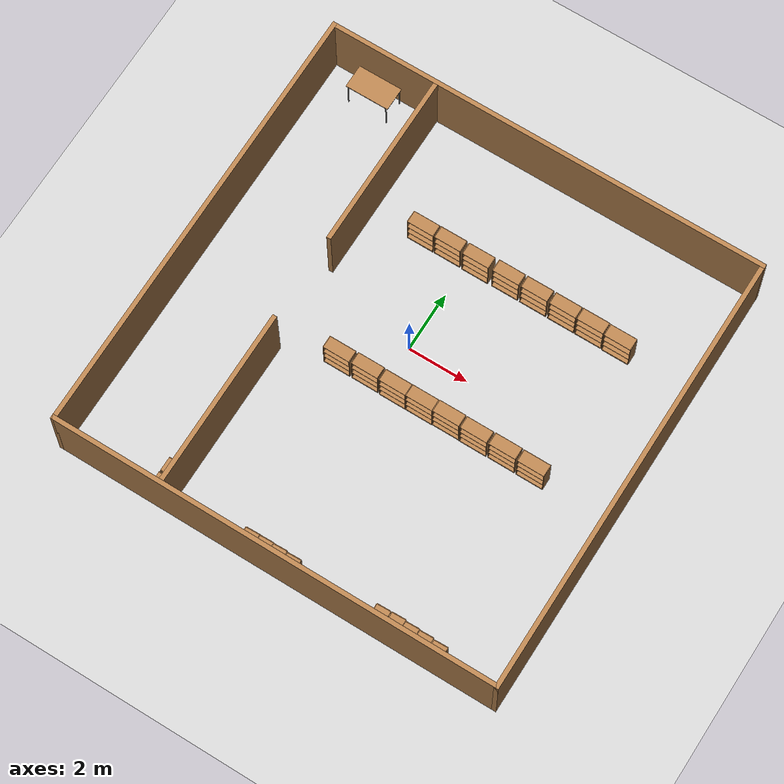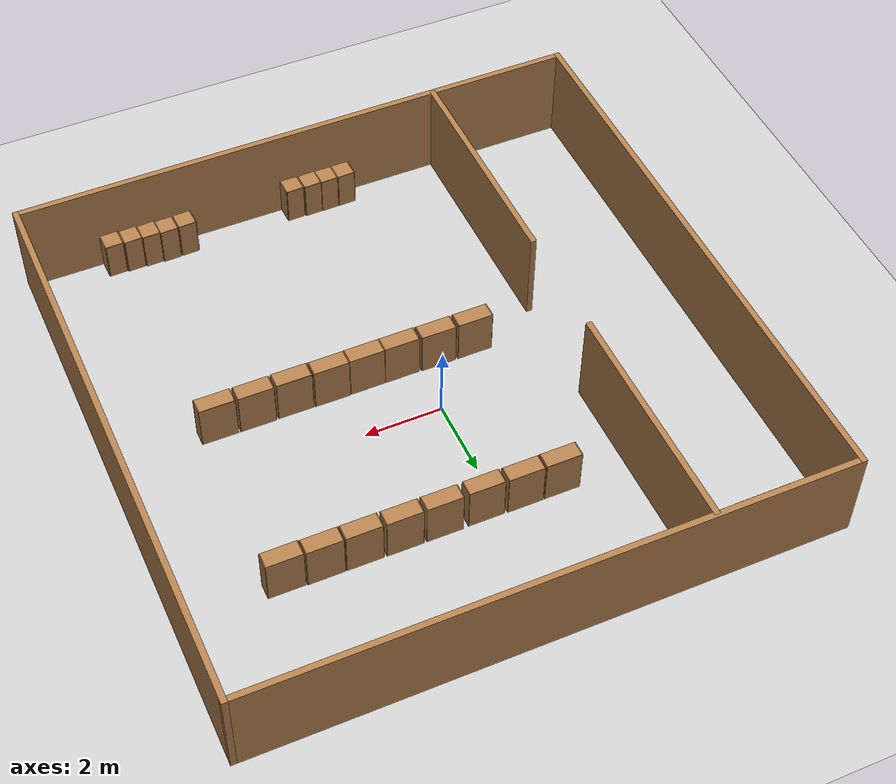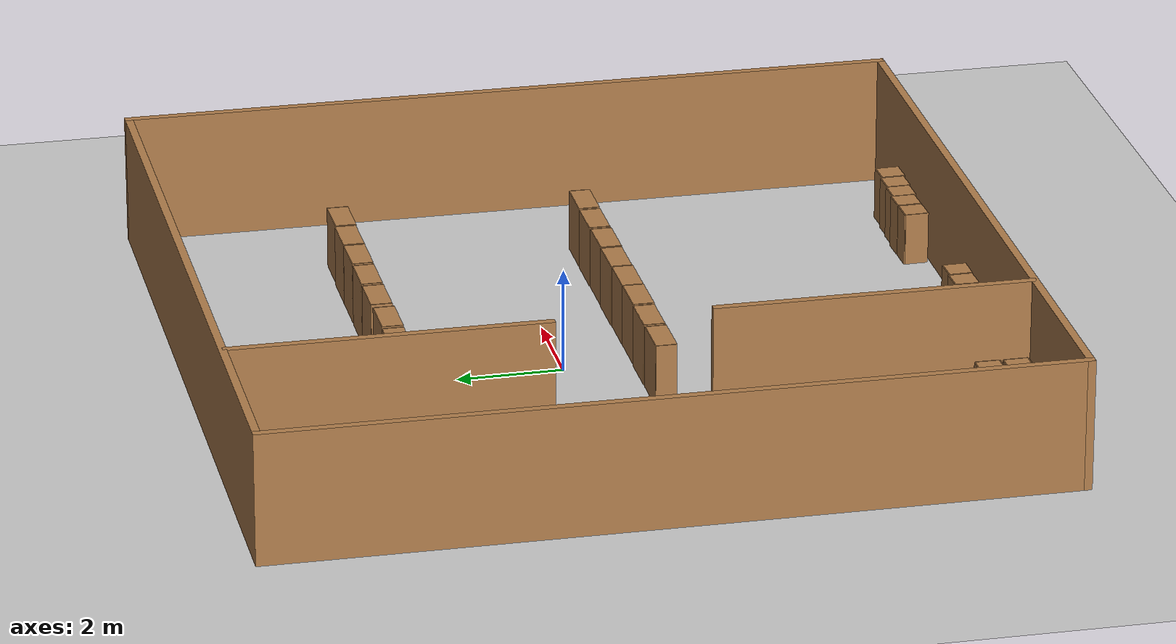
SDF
<sdf version="1.7">
 <world name="default">
  <light name="sun" type="directional">
   <pose>0 0 10 0 -0 0</pose>
   <diffuse>0.8 0.8 0.8 1</diffuse>
   <specular>0.2 0.2 0.2 1</specular>
   <attenuation>
    <range>1000</range>
    <constant>0.9</constant>
    <linear>0.01</linear>
    <quadratic>0.001</quadratic>
   </attenuation>
   <direction>-0.5 0.1 -0.9</direction>
   <spot><inner_angle>0</inner_angle><outer_angle>0</outer_angle><falloff>0</falloff></spot>
  </light>
  <model name="ground_plane">
   <static>1</static>
   <link name="link">
    <collision name="collision">
     <geometry><plane><normal>0 0 1</normal><size>100 100</size></plane></geometry>
     <surface>
      <contact><collide_bitmask>65535</collide_bitmask></contact>
      <friction><ode><mu>100</mu><mu2>50</mu2></ode></friction>
     </surface>
    </collision>
    <visual name="visual">
     <cast_shadows>0</cast_shadows>
     <geometry><plane><normal>0 0 1</normal><size>100 100</size></plane></geometry>
     <material>
      <script><uri>file://media/materials/scripts/gazebo.material</uri><name>Gazebo/Grey</name></script>
     </material>
    </visual>
   </link>
  </model>
  <gravity>0 0 -9.8</gravity>
  <magnetic_field>6e-06 2.3e-05 -4.2e-05</magnetic_field>
  <atmosphere type="adiabatic"/>
  <physics type="ode">
   <max_step_size>0.001</max_step_size>
   <real_time_factor>1</real_time_factor>
   <real_time_update_rate>10.0</real_time_update_rate>
  </physics>
  <scene><ambient>0.4 0.4 0.4 1</ambient><background>0.7 0.7 0.7 1</background><shadows>1</shadows></scene>
  <spherical_coordinates>
   <surface_model>EARTH_WGS84</surface_model>
   <latitude_deg>0</latitude_deg>
   <longitude_deg>0</longitude_deg>
   <elevation>0</elevation>
   <heading_deg>0</heading_deg>
  </spherical_coordinates>
  <model name="lmao1_0">
   <pose>0.44681 -0.57627 0 0 -0 0</pose>
   <link name="Wall_10">
    <collision name="Wall_10_Collision">
     <geometry><box><size>15 0.15 2.5</size></box></geometry>
     <pose>0 0 1.25 0 -0 0</pose>
    </collision>
    <visual name="Wall_10_Visual">
     <pose>0 0 1.25 0 -0 0</pose>
     <geometry><box><size>15 0.15 2.5</size></box></geometry>
     <material>
      <script><uri>file://media/materials/scripts/gazebo.material</uri><name>Gazebo/Wood</name></script>
      <ambient>1 1 1 1</ambient>
     </material>
     <meta><layer>0</layer></meta>
    </visual>
    <pose>7.425 0 0 0 -0 1.5708</pose>
   </link>
   <link name="Wall_12">
    <collision name="Wall_12_Collision">
     <geometry><box><size>15 0.15 2.5</size></box></geometry>
     <pose>0 0 1.25 0 -0 0</pose>
    </collision>
    <visual name="Wall_12_Visual">
     <pose>0 0 1.25 0 -0 0</pose>
     <geometry><box><size>15 0.15 2.5</size></box></geometry>
     <material>
      <script><uri>file://media/materials/scripts/gazebo.material</uri><name>Gazebo/Wood</name></script>
      <ambient>1 1 1 1</ambient>
     </material>
     <meta><layer>0</layer></meta>
    </visual>
    <pose>0 7.425 0 0 -0 3.14159</pose>
   </link>
   <link name="Wall_14">
    <collision name="Wall_14_Collision">
     <geometry><box><size>15 0.15 2.5</size></box></geometry>
     <pose>0 0 1.25 0 -0 0</pose>
    </collision>
    <visual name="Wall_14_Visual">
     <pose>0 0 1.25 0 -0 0</pose>
     <geometry><box><size>15 0.15 2.5</size></box></geometry>
     <material>
      <script><uri>file://media/materials/scripts/gazebo.material</uri><name>Gazebo/Wood</name></script>
      <ambient>1 1 1 1</ambient>
     </material>
     <meta><layer>0</layer></meta>
    </visual>
    <pose>-7.425 0 0 0 -0 1.5708</pose>
   </link>
   <link name="Wall_16">
    <collision name="Wall_16_Collision">
     <geometry><box><size>6 0.15 2.5</size></box></geometry>
     <pose>0 0 1.25 0 -0 0</pose>
    </collision>
    <visual name="Wall_16_Visual">
     <pose>0 0 1.25 0 -0 0</pose>
     <geometry><box><size>6 0.15 2.5</size></box></geometry>
     <material>
      <script><uri>file://media/materials/scripts/gazebo.material</uri><name>Gazebo/Wood</name></script>
      <ambient>1 1 1 1</ambient>
     </material>
     <meta><layer>0</layer></meta>
    </visual>
    <pose>-3.77777 4.42781 0 0 -0 -1.5708</pose>
   </link>
   <link name="Wall_21">
    <collision name="Wall_21_Collision">
     <geometry><box><size>6 0.15 2.5</size></box></geometry>
     <pose>0 0 1.25 0 -0 0</pose>
    </collision>
    <visual name="Wall_21_Visual">
     <pose>0 0 1.25 0 -0 0</pose>
     <geometry><box><size>6 0.15 2.5</size></box></geometry>
     <material>
      <script><uri>file://media/materials/scripts/gazebo.material</uri><name>Gazebo/Wood</name></script>
      <ambient>1 1 1 1</ambient>
     </material>
     <meta><layer>0</layer></meta>
    </visual>
    <pose>-3.77777 -4.44802 0 0 -0 1.5708</pose>
   </link>
   <link name="Wall_8">
    <collision name="Wall_8_Collision">
     <geometry><box><size>15 0.15 2.5</size></box></geometry>
     <pose>0 0 1.25 0 -0 0</pose>
    </collision>
    <visual name="Wall_8_Visual">
     <pose>0 0 1.25 0 -0 0</pose>
     <geometry><box><size>15 0.15 2.5</size></box></geometry>
     <material>
      <script><uri>file://media/materials/scripts/gazebo.material</uri><name>Gazebo/Wood</name></script>
      <ambient>1 1 1 1</ambient>
     </material>
     <meta><layer>0</layer></meta>
    </visual>
    <pose>0 -7.425 0 0 -0 0</pose>
   </link>
   <static>1</static>
  </model>
  <model name="table">
   <static>1</static>
   <link name="link">
    <collision name="surface">
     <pose>0 0 1 0 -0 0</pose>
     <geometry><box><size>1.5 0.8 0.03</size></box></geometry>
     <surface><friction><ode><mu>0.6</mu><mu2>0.6</mu2></ode></friction></surface>
    </collision>
    <visual name="visual1">
     <pose>0 0 1 0 -0 0</pose>
     <geometry><box><size>1.5 0.8 0.03</size></box></geometry>
     <material>
      <script><uri>file://media/materials/scripts/gazebo.material</uri><name>Gazebo/Wood</name></script>
     </material>
    </visual>
    <collision name="front_left_leg">
     <pose>0.68 0.38 0.5 0 -0 0</pose>
     <geometry><cylinder><radius>0.02</radius><length>1</length></cylinder></geometry>
    </collision>
    <visual name="front_left_leg">
     <pose>0.68 0.38 0.5 0 -0 0</pose>
     <geometry><cylinder><radius>0.02</radius><length>1</length></cylinder></geometry>
     <material>
      <script><uri>file://media/materials/scripts/gazebo.material</uri><name>Gazebo/Grey</name></script>
     </material>
    </visual>
    <collision name="front_right_leg">
     <pose>0.68 -0.38 0.5 0 -0 0</pose>
     <geometry><cylinder><radius>0.02</radius><length>1</length></cylinder></geometry>
    </collision>
    <visual name="front_right_leg">
     <pose>0.68 -0.38 0.5 0 -0 0</pose>
     <geometry><cylinder><radius>0.02</radius><length>1</length></cylinder></geometry>
     <material>
      <script><uri>file://media/materials/scripts/gazebo.material</uri><name>Gazebo/Grey</name></script>
     </material>
    </visual>
    <collision name="back_right_leg">
     <pose>-0.68 -0.38 0.5 0 -0 0</pose>
     <geometry><cylinder><radius>0.02</radius><length>1</length></cylinder></geometry>
    </collision>
    <visual name="back_right_leg">
     <pose>-0.68 -0.38 0.5 0 -0 0</pose>
     <geometry><cylinder><radius>0.02</radius><length>1</length></cylinder></geometry>
     <material>
      <script><uri>file://media/materials/scripts/gazebo.material</uri><name>Gazebo/Grey</name></script>
     </material>
    </visual>
    <collision name="back_left_leg">
     <pose>-0.68 0.38 0.5 0 -0 0</pose>
     <geometry><cylinder><radius>0.02</radius><length>1</length></cylinder></geometry>
    </collision>
    <visual name="back_left_leg">
     <pose>-0.68 0.38 0.5 0 -0 0</pose>
     <geometry><cylinder><radius>0.02</radius><length>1</length></cylinder></geometry>
     <material>
      <script><uri>file://media/materials/scripts/gazebo.material</uri><name>Gazebo/Grey</name></script>
     </material>
    </visual>
   </link>
   <pose>-5.24151 6.30081 0 0 -0 0</pose>
  </model>
  <model name="cabinet">
   <static>1</static>
   <link name="cabinet_bottom_plate">
    <inertial>
     <pose>0 0 -1 0 -0 0</pose>
     <inertia><ixx>2.05</ixx><ixy>0</ixy><ixz>0</ixz><iyy>2.05</iyy><iyz>0</iyz><izz>2.05</izz></inertia>
     <mass>25</mass>
    </inertial>
    <collision name="cabinet_bottom_plate_geom">
     <pose>0 0 0.01 0 -0 0</pose>
     <geometry><box><size>0.45 0.45 0.02</size></box></geometry>
    </collision>
    <visual name="cabinet_bottom_plate_geom_visual">
     <pose>0 0 0.01 0 -0 0</pose>
     <geometry><box><size>0.45 0.45 0.02</size></box></geometry>
     <material>
      <script><uri>file://media/materials/scripts/gazebo.material</uri><name>Gazebo/Wood</name></script>
     </material>
    </visual>
    <collision name="cabinet_bottom_plate_geom_cabinet_back_plate">
     <pose>0.235 0 0.51 0 -0 0</pose>
     <geometry><box><size>0.02 0.45 1.02</size></box></geometry>
    </collision>
    <visual name="cabinet_bottom_plate_geom_cabinet_back_plate_visual">
     <pose>0.235 0 0.51 0 -0 0</pose>
     <geometry><box><size>0.02 0.45 1.02</size></box></geometry>
     <material>
      <script><uri>file://media/materials/scripts/gazebo.material</uri><name>Gazebo/Wood</name></script>
     </material>
    </visual>
    <collision name="cabinet_bottom_plate_geom_cabinet_left_plate">
     <pose>0 0.235 0.51 0 -0 0</pose>
     <geometry><box><size>0.45 0.02 1.02</size></box></geometry>
    </collision>
    <visual name="cabinet_bottom_plate_geom_cabinet_left_plate_visual">
     <pose>0 0.235 0.51 0 -0 0</pose>
     <geometry><box><size>0.45 0.02 1.02</size></box></geometry>
     <material>
      <script><uri>file://media/materials/scripts/gazebo.material</uri><name>Gazebo/Wood</name></script>
     </material>
    </visual>
    <collision name="cabinet_bottom_plate_geom_cabinet_middle_plate">
     <pose>0 0 0.51 0 -0 0</pose>
     <geometry><box><size>0.45 0.45 0.02</size></box></geometry>
    </collision>
    <visual name="cabinet_bottom_plate_geom_cabinet_middle_plate_visual">
     <pose>0 0 0.51 0 -0 0</pose>
     <geometry><box><size>0.45 0.45 0.02</size></box></geometry>
     <material>
      <script><uri>file://media/materials/scripts/gazebo.material</uri><name>Gazebo/Wood</name></script>
     </material>
    </visual>
    <collision name="cabinet_bottom_plate_geom_cabinet_right_plate">
     <pose>0 -0.235 0.51 0 -0 0</pose>
     <geometry><box><size>0.45 0.02 1.02</size></box></geometry>
    </collision>
    <visual name="cabinet_bottom_plate_geom_cabinet_right_plate_visual">
     <pose>0 -0.235 0.51 0 -0 0</pose>
     <geometry><box><size>0.45 0.02 1.02</size></box></geometry>
     <material>
      <script><uri>file://media/materials/scripts/gazebo.material</uri><name>Gazebo/Wood</name></script>
     </material>
    </visual>
    <collision name="cabinet_bottom_plate_geom_cabinet_top_plate">
     <pose>0 0 1.01 0 -0 0</pose>
     <geometry><box><size>0.45 0.45 0.02</size></box></geometry>
    </collision>
    <visual name="cabinet_bottom_plate_geom_cabinet_top_plate_visual">
     <pose>0 0 1.01 0 -0 0</pose>
     <geometry><box><size>0.45 0.45 0.02</size></box></geometry>
     <material>
      <script><uri>file://media/materials/scripts/gazebo.material</uri><name>Gazebo/Wood</name></script>
     </material>
    </visual>
   </link>
   <pose>-3.67458 -7.64676 0 0 -0 0</pose>
  </model>
  <model name="cabinet_clone">
   <static>1</static>
   <link name="cabinet_bottom_plate">
    <inertial>
     <pose>0 0 -1 0 -0 0</pose>
     <inertia><ixx>2.05</ixx><ixy>0</ixy><ixz>0</ixz><iyy>2.05</iyy><iyz>0</iyz><izz>2.05</izz></inertia>
     <mass>25</mass>
    </inertial>
    <collision name="cabinet_bottom_plate_geom">
     <pose>0 0 0.01 0 -0 0</pose>
     <geometry><box><size>0.45 0.45 0.02</size></box></geometry>
    </collision>
    <visual name="cabinet_bottom_plate_geom_visual">
     <pose>0 0 0.01 0 -0 0</pose>
     <geometry><box><size>0.45 0.45 0.02</size></box></geometry>
     <material>
      <script><uri>file://media/materials/scripts/gazebo.material</uri><name>Gazebo/Wood</name></script>
     </material>
    </visual>
    <collision name="cabinet_bottom_plate_geom_cabinet_back_plate">
     <pose>0.235 0 0.51 0 -0 0</pose>
     <geometry><box><size>0.02 0.45 1.02</size></box></geometry>
    </collision>
    <visual name="cabinet_bottom_plate_geom_cabinet_back_plate_visual">
     <pose>0.235 0 0.51 0 -0 0</pose>
     <geometry><box><size>0.02 0.45 1.02</size></box></geometry>
     <material>
      <script><uri>file://media/materials/scripts/gazebo.material</uri><name>Gazebo/Wood</name></script>
     </material>
    </visual>
    <collision name="cabinet_bottom_plate_geom_cabinet_left_plate">
     <pose>0 0.235 0.51 0 -0 0</pose>
     <geometry><box><size>0.45 0.02 1.02</size></box></geometry>
    </collision>
    <visual name="cabinet_bottom_plate_geom_cabinet_left_plate_visual">
     <pose>0 0.235 0.51 0 -0 0</pose>
     <geometry><box><size>0.45 0.02 1.02</size></box></geometry>
     <material>
      <script><uri>file://media/materials/scripts/gazebo.material</uri><name>Gazebo/Wood</name></script>
     </material>
    </visual>
    <collision name="cabinet_bottom_plate_geom_cabinet_middle_plate">
     <pose>0 0 0.51 0 -0 0</pose>
     <geometry><box><size>0.45 0.45 0.02</size></box></geometry>
    </collision>
    <visual name="cabinet_bottom_plate_geom_cabinet_middle_plate_visual">
     <pose>0 0 0.51 0 -0 0</pose>
     <geometry><box><size>0.45 0.45 0.02</size></box></geometry>
     <material>
      <script><uri>file://media/materials/scripts/gazebo.material</uri><name>Gazebo/Wood</name></script>
     </material>
    </visual>
    <collision name="cabinet_bottom_plate_geom_cabinet_right_plate">
     <pose>0 -0.235 0.51 0 -0 0</pose>
     <geometry><box><size>0.45 0.02 1.02</size></box></geometry>
    </collision>
    <visual name="cabinet_bottom_plate_geom_cabinet_right_plate_visual">
     <pose>0 -0.235 0.51 0 -0 0</pose>
     <geometry><box><size>0.45 0.02 1.02</size></box></geometry>
     <material>
      <script><uri>file://media/materials/scripts/gazebo.material</uri><name>Gazebo/Wood</name></script>
     </material>
    </visual>
    <collision name="cabinet_bottom_plate_geom_cabinet_top_plate">
     <pose>0 0 1.01 0 -0 0</pose>
     <geometry><box><size>0.45 0.45 0.02</size></box></geometry>
    </collision>
    <visual name="cabinet_bottom_plate_geom_cabinet_top_plate_visual">
     <pose>0 0 1.01 0 -0 0</pose>
     <geometry><box><size>0.45 0.45 0.02</size></box></geometry>
     <material>
      <script><uri>file://media/materials/scripts/gazebo.material</uri><name>Gazebo/Wood</name></script>
     </material>
    </visual>
   </link>
   <pose>-3.66557 -7.11743 0 0 -0 0</pose>
  </model>
  <model name="bookshelf">
   <static>1</static>
   <link name="link">
    <inertial><mass>1</mass></inertial>
    <collision name="back">
     <pose>0 0.005 0.6 0 -0 0</pose>
     <geometry><box><size>0.9 0.01 1.2</size></box></geometry>
    </collision>
    <visual name="visual1">
     <pose>0 0.005 0.6 0 -0 0</pose>
     <geometry><box><size>0.9 0.01 1.2</size></box></geometry>
     <material>
      <script><uri>file://media/materials/scripts/gazebo.material</uri><name>Gazebo/Wood</name></script>
     </material>
    </visual>
    <collision name="left_side">
     <pose>0.45 -0.195 0.6 0 -0 0</pose>
     <geometry><box><size>0.02 0.4 1.2</size></box></geometry>
    </collision>
    <visual name="visual2">
     <pose>0.45 -0.195 0.6 0 -0 0</pose>
     <geometry><box><size>0.02 0.4 1.2</size></box></geometry>
     <material>
      <script><uri>file://media/materials/scripts/gazebo.material</uri><name>Gazebo/Wood</name></script>
     </material>
    </visual>
    <collision name="right_side">
     <pose>-0.45 -0.195 0.6 0 -0 0</pose>
     <geometry><box><size>0.02 0.4 1.2</size></box></geometry>
    </collision>
    <visual name="visual3">
     <pose>-0.45 -0.195 0.6 0 -0 0</pose>
     <geometry><box><size>0.02 0.4 1.2</size></box></geometry>
     <material>
      <script><uri>file://media/materials/scripts/gazebo.material</uri><name>Gazebo/Wood</name></script>
     </material>
    </visual>
    <collision name="bottom">
     <pose>0 -0.195 0.03 0 -0 0</pose>
     <geometry><box><size>0.88 0.4 0.06</size></box></geometry>
    </collision>
    <visual name="visual4">
     <pose>0 -0.195 0.03 0 -0 0</pose>
     <geometry><box><size>0.88 0.4 0.06</size></box></geometry>
     <material>
      <script><uri>file://media/materials/scripts/gazebo.material</uri><name>Gazebo/Wood</name></script>
     </material>
    </visual>
    <collision name="top">
     <pose>0 -0.195 1.19 0 -0 0</pose>
     <geometry><box><size>0.88 0.4 0.02</size></box></geometry>
    </collision>
    <visual name="visual5">
     <pose>0 -0.195 1.19 0 -0 0</pose>
     <geometry><box><size>0.88 0.4 0.02</size></box></geometry>
     <material>
      <script><uri>file://media/materials/scripts/gazebo.material</uri><name>Gazebo/Wood</name></script>
     </material>
    </visual>
    <collision name="low_shelf">
     <pose>0 -0.195 0.43 0 -0 0</pose>
     <geometry><box><size>0.88 0.4 0.02</size></box></geometry>
    </collision>
    <visual name="visual6">
     <pose>0 -0.195 0.43 0 -0 0</pose>
     <geometry><box><size>0.88 0.4 0.02</size></box></geometry>
     <material>
      <script><uri>file://media/materials/scripts/gazebo.material</uri><name>Gazebo/Wood</name></script>
     </material>
    </visual>
    <collision name="high_shelf">
     <pose>0 -0.195 0.8 0 -0 0</pose>
     <geometry><box><size>0.88 0.4 0.02</size></box></geometry>
    </collision>
    <visual name="visual7">
     <pose>0 -0.195 0.8 0 -0 0</pose>
     <geometry><box><size>0.88 0.4 0.02</size></box></geometry>
     <material>
      <script><uri>file://media/materials/scripts/gazebo.material</uri><name>Gazebo/Wood</name></script>
     </material>
    </visual>
   </link>
   <pose>-1.517 3.39821 0.008039 0 -0 0</pose>
  </model>
  <model name="bookshelf_clone">
   <static>1</static>
   <link name="link">
    <inertial><mass>1</mass></inertial>
    <collision name="back">
     <pose>0 0.005 0.6 0 -0 0</pose>
     <geometry><box><size>0.9 0.01 1.2</size></box></geometry>
    </collision>
    <visual name="visual1">
     <pose>0 0.005 0.6 0 -0 0</pose>
     <geometry><box><size>0.9 0.01 1.2</size></box></geometry>
     <material>
      <script><uri>file://media/materials/scripts/gazebo.material</uri><name>Gazebo/Wood</name></script>
     </material>
    </visual>
    <collision name="left_side">
     <pose>0.45 -0.195 0.6 0 -0 0</pose>
     <geometry><box><size>0.02 0.4 1.2</size></box></geometry>
    </collision>
    <visual name="visual2">
     <pose>0.45 -0.195 0.6 0 -0 0</pose>
     <geometry><box><size>0.02 0.4 1.2</size></box></geometry>
     <material>
      <script><uri>file://media/materials/scripts/gazebo.material</uri><name>Gazebo/Wood</name></script>
     </material>
    </visual>
    <collision name="right_side">
     <pose>-0.45 -0.195 0.6 0 -0 0</pose>
     <geometry><box><size>0.02 0.4 1.2</size></box></geometry>
    </collision>
    <visual name="visual3">
     <pose>-0.45 -0.195 0.6 0 -0 0</pose>
     <geometry><box><size>0.02 0.4 1.2</size></box></geometry>
     <material>
      <script><uri>file://media/materials/scripts/gazebo.material</uri><name>Gazebo/Wood</name></script>
     </material>
    </visual>
    <collision name="bottom">
     <pose>0 -0.195 0.03 0 -0 0</pose>
     <geometry><box><size>0.88 0.4 0.06</size></box></geometry>
    </collision>
    <visual name="visual4">
     <pose>0 -0.195 0.03 0 -0 0</pose>
     <geometry><box><size>0.88 0.4 0.06</size></box></geometry>
     <material>
      <script><uri>file://media/materials/scripts/gazebo.material</uri><name>Gazebo/Wood</name></script>
     </material>
    </visual>
    <collision name="top">
     <pose>0 -0.195 1.19 0 -0 0</pose>
     <geometry><box><size>0.88 0.4 0.02</size></box></geometry>
    </collision>
    <visual name="visual5">
     <pose>0 -0.195 1.19 0 -0 0</pose>
     <geometry><box><size>0.88 0.4 0.02</size></box></geometry>
     <material>
      <script><uri>file://media/materials/scripts/gazebo.material</uri><name>Gazebo/Wood</name></script>
     </material>
    </visual>
    <collision name="low_shelf">
     <pose>0 -0.195 0.43 0 -0 0</pose>
     <geometry><box><size>0.88 0.4 0.02</size></box></geometry>
    </collision>
    <visual name="visual6">
     <pose>0 -0.195 0.43 0 -0 0</pose>
     <geometry><box><size>0.88 0.4 0.02</size></box></geometry>
     <material>
      <script><uri>file://media/materials/scripts/gazebo.material</uri><name>Gazebo/Wood</name></script>
     </material>
    </visual>
    <collision name="high_shelf">
     <pose>0 -0.195 0.8 0 -0 0</pose>
     <geometry><box><size>0.88 0.4 0.02</size></box></geometry>
    </collision>
    <visual name="visual7">
     <pose>0 -0.195 0.8 0 -0 0</pose>
     <geometry><box><size>0.88 0.4 0.02</size></box></geometry>
     <material>
      <script><uri>file://media/materials/scripts/gazebo.material</uri><name>Gazebo/Wood</name></script>
     </material>
    </visual>
   </link>
   <pose>-0.568869 3.40329 0.008039 0 -0 0</pose>
  </model>
  <model name="bookshelf_clone_0">
   <static>1</static>
   <link name="link">
    <inertial><mass>1</mass></inertial>
    <collision name="back">
     <pose>0 0.005 0.6 0 -0 0</pose>
     <geometry><box><size>0.9 0.01 1.2</size></box></geometry>
    </collision>
    <visual name="visual1">
     <pose>0 0.005 0.6 0 -0 0</pose>
     <geometry><box><size>0.9 0.01 1.2</size></box></geometry>
     <material>
      <script><uri>file://media/materials/scripts/gazebo.material</uri><name>Gazebo/Wood</name></script>
     </material>
    </visual>
    <collision name="left_side">
     <pose>0.45 -0.195 0.6 0 -0 0</pose>
     <geometry><box><size>0.02 0.4 1.2</size></box></geometry>
    </collision>
    <visual name="visual2">
     <pose>0.45 -0.195 0.6 0 -0 0</pose>
     <geometry><box><size>0.02 0.4 1.2</size></box></geometry>
     <material>
      <script><uri>file://media/materials/scripts/gazebo.material</uri><name>Gazebo/Wood</name></script>
     </material>
    </visual>
    <collision name="right_side">
     <pose>-0.45 -0.195 0.6 0 -0 0</pose>
     <geometry><box><size>0.02 0.4 1.2</size></box></geometry>
    </collision>
    <visual name="visual3">
     <pose>-0.45 -0.195 0.6 0 -0 0</pose>
     <geometry><box><size>0.02 0.4 1.2</size></box></geometry>
     <material>
      <script><uri>file://media/materials/scripts/gazebo.material</uri><name>Gazebo/Wood</name></script>
     </material>
    </visual>
    <collision name="bottom">
     <pose>0 -0.195 0.03 0 -0 0</pose>
     <geometry><box><size>0.88 0.4 0.06</size></box></geometry>
    </collision>
    <visual name="visual4">
     <pose>0 -0.195 0.03 0 -0 0</pose>
     <geometry><box><size>0.88 0.4 0.06</size></box></geometry>
     <material>
      <script><uri>file://media/materials/scripts/gazebo.material</uri><name>Gazebo/Wood</name></script>
     </material>
    </visual>
    <collision name="top">
     <pose>0 -0.195 1.19 0 -0 0</pose>
     <geometry><box><size>0.88 0.4 0.02</size></box></geometry>
    </collision>
    <visual name="visual5">
     <pose>0 -0.195 1.19 0 -0 0</pose>
     <geometry><box><size>0.88 0.4 0.02</size></box></geometry>
     <material>
      <script><uri>file://media/materials/scripts/gazebo.material</uri><name>Gazebo/Wood</name></script>
     </material>
    </visual>
    <collision name="low_shelf">
     <pose>0 -0.195 0.43 0 -0 0</pose>
     <geometry><box><size>0.88 0.4 0.02</size></box></geometry>
    </collision>
    <visual name="visual6">
     <pose>0 -0.195 0.43 0 -0 0</pose>
     <geometry><box><size>0.88 0.4 0.02</size></box></geometry>
     <material>
      <script><uri>file://media/materials/scripts/gazebo.material</uri><name>Gazebo/Wood</name></script>
     </material>
    </visual>
    <collision name="high_shelf">
     <pose>0 -0.195 0.8 0 -0 0</pose>
     <geometry><box><size>0.88 0.4 0.02</size></box></geometry>
    </collision>
    <visual name="visual7">
     <pose>0 -0.195 0.8 0 -0 0</pose>
     <geometry><box><size>0.88 0.4 0.02</size></box></geometry>
     <material>
      <script><uri>file://media/materials/scripts/gazebo.material</uri><name>Gazebo/Wood</name></script>
     </material>
    </visual>
   </link>
   <pose>0.417185 3.39118 0.008039 0 -0 0</pose>
  </model>
  <model name="bookshelf_clone_1">
   <static>1</static>
   <link name="link">
    <inertial><mass>1</mass></inertial>
    <collision name="back">
     <pose>0 0.005 0.6 0 -0 0</pose>
     <geometry><box><size>0.9 0.01 1.2</size></box></geometry>
    </collision>
    <visual name="visual1">
     <pose>0 0.005 0.6 0 -0 0</pose>
     <geometry><box><size>0.9 0.01 1.2</size></box></geometry>
     <material>
      <script><uri>file://media/materials/scripts/gazebo.material</uri><name>Gazebo/Wood</name></script>
     </material>
    </visual>
    <collision name="left_side">
     <pose>0.45 -0.195 0.6 0 -0 0</pose>
     <geometry><box><size>0.02 0.4 1.2</size></box></geometry>
    </collision>
    <visual name="visual2">
     <pose>0.45 -0.195 0.6 0 -0 0</pose>
     <geometry><box><size>0.02 0.4 1.2</size></box></geometry>
     <material>
      <script><uri>file://media/materials/scripts/gazebo.material</uri><name>Gazebo/Wood</name></script>
     </material>
    </visual>
    <collision name="right_side">
     <pose>-0.45 -0.195 0.6 0 -0 0</pose>
     <geometry><box><size>0.02 0.4 1.2</size></box></geometry>
    </collision>
    <visual name="visual3">
     <pose>-0.45 -0.195 0.6 0 -0 0</pose>
     <geometry><box><size>0.02 0.4 1.2</size></box></geometry>
     <material>
      <script><uri>file://media/materials/scripts/gazebo.material</uri><name>Gazebo/Wood</name></script>
     </material>
    </visual>
    <collision name="bottom">
     <pose>0 -0.195 0.03 0 -0 0</pose>
     <geometry><box><size>0.88 0.4 0.06</size></box></geometry>
    </collision>
    <visual name="visual4">
     <pose>0 -0.195 0.03 0 -0 0</pose>
     <geometry><box><size>0.88 0.4 0.06</size></box></geometry>
     <material>
      <script><uri>file://media/materials/scripts/gazebo.material</uri><name>Gazebo/Wood</name></script>
     </material>
    </visual>
    <collision name="top">
     <pose>0 -0.195 1.19 0 -0 0</pose>
     <geometry><box><size>0.88 0.4 0.02</size></box></geometry>
    </collision>
    <visual name="visual5">
     <pose>0 -0.195 1.19 0 -0 0</pose>
     <geometry><box><size>0.88 0.4 0.02</size></box></geometry>
     <material>
      <script><uri>file://media/materials/scripts/gazebo.material</uri><name>Gazebo/Wood</name></script>
     </material>
    </visual>
    <collision name="low_shelf">
     <pose>0 -0.195 0.43 0 -0 0</pose>
     <geometry><box><size>0.88 0.4 0.02</size></box></geometry>
    </collision>
    <visual name="visual6">
     <pose>0 -0.195 0.43 0 -0 0</pose>
     <geometry><box><size>0.88 0.4 0.02</size></box></geometry>
     <material>
      <script><uri>file://media/materials/scripts/gazebo.material</uri><name>Gazebo/Wood</name></script>
     </material>
    </visual>
    <collision name="high_shelf">
     <pose>0 -0.195 0.8 0 -0 0</pose>
     <geometry><box><size>0.88 0.4 0.02</size></box></geometry>
    </collision>
    <visual name="visual7">
     <pose>0 -0.195 0.8 0 -0 0</pose>
     <geometry><box><size>0.88 0.4 0.02</size></box></geometry>
     <material>
      <script><uri>file://media/materials/scripts/gazebo.material</uri><name>Gazebo/Wood</name></script>
     </material>
    </visual>
   </link>
   <pose>1.46048 3.40395 0.008039 0 -0 0</pose>
  </model>
  <model name="bookshelf_clone_2">
   <static>1</static>
   <link name="link">
    <inertial><mass>1</mass></inertial>
    <collision name="back">
     <pose>0 0.005 0.6 0 -0 0</pose>
     <geometry><box><size>0.9 0.01 1.2</size></box></geometry>
    </collision>
    <visual name="visual1">
     <pose>0 0.005 0.6 0 -0 0</pose>
     <geometry><box><size>0.9 0.01 1.2</size></box></geometry>
     <material>
      <script><uri>file://media/materials/scripts/gazebo.material</uri><name>Gazebo/Wood</name></script>
     </material>
    </visual>
    <collision name="left_side">
     <pose>0.45 -0.195 0.6 0 -0 0</pose>
     <geometry><box><size>0.02 0.4 1.2</size></box></geometry>
    </collision>
    <visual name="visual2">
     <pose>0.45 -0.195 0.6 0 -0 0</pose>
     <geometry><box><size>0.02 0.4 1.2</size></box></geometry>
     <material>
      <script><uri>file://media/materials/scripts/gazebo.material</uri><name>Gazebo/Wood</name></script>
     </material>
    </visual>
    <collision name="right_side">
     <pose>-0.45 -0.195 0.6 0 -0 0</pose>
     <geometry><box><size>0.02 0.4 1.2</size></box></geometry>
    </collision>
    <visual name="visual3">
     <pose>-0.45 -0.195 0.6 0 -0 0</pose>
     <geometry><box><size>0.02 0.4 1.2</size></box></geometry>
     <material>
      <script><uri>file://media/materials/scripts/gazebo.material</uri><name>Gazebo/Wood</name></script>
     </material>
    </visual>
    <collision name="bottom">
     <pose>0 -0.195 0.03 0 -0 0</pose>
     <geometry><box><size>0.88 0.4 0.06</size></box></geometry>
    </collision>
    <visual name="visual4">
     <pose>0 -0.195 0.03 0 -0 0</pose>
     <geometry><box><size>0.88 0.4 0.06</size></box></geometry>
     <material>
      <script><uri>file://media/materials/scripts/gazebo.material</uri><name>Gazebo/Wood</name></script>
     </material>
    </visual>
    <collision name="top">
     <pose>0 -0.195 1.19 0 -0 0</pose>
     <geometry><box><size>0.88 0.4 0.02</size></box></geometry>
    </collision>
    <visual name="visual5">
     <pose>0 -0.195 1.19 0 -0 0</pose>
     <geometry><box><size>0.88 0.4 0.02</size></box></geometry>
     <material>
      <script><uri>file://media/materials/scripts/gazebo.material</uri><name>Gazebo/Wood</name></script>
     </material>
    </visual>
    <collision name="low_shelf">
     <pose>0 -0.195 0.43 0 -0 0</pose>
     <geometry><box><size>0.88 0.4 0.02</size></box></geometry>
    </collision>
    <visual name="visual6">
     <pose>0 -0.195 0.43 0 -0 0</pose>
     <geometry><box><size>0.88 0.4 0.02</size></box></geometry>
     <material>
      <script><uri>file://media/materials/scripts/gazebo.material</uri><name>Gazebo/Wood</name></script>
     </material>
    </visual>
    <collision name="high_shelf">
     <pose>0 -0.195 0.8 0 -0 0</pose>
     <geometry><box><size>0.88 0.4 0.02</size></box></geometry>
    </collision>
    <visual name="visual7">
     <pose>0 -0.195 0.8 0 -0 0</pose>
     <geometry><box><size>0.88 0.4 0.02</size></box></geometry>
     <material>
      <script><uri>file://media/materials/scripts/gazebo.material</uri><name>Gazebo/Wood</name></script>
     </material>
    </visual>
   </link>
   <pose>2.44199 3.40428 0.008039 0 -0 0</pose>
  </model>
  <model name="bookshelf_clone_3">
   <static>1</static>
   <link name="link">
    <inertial><mass>1</mass></inertial>
    <collision name="back">
     <pose>0 0.005 0.6 0 -0 0</pose>
     <geometry><box><size>0.9 0.01 1.2</size></box></geometry>
    </collision>
    <visual name="visual1">
     <pose>0 0.005 0.6 0 -0 0</pose>
     <geometry><box><size>0.9 0.01 1.2</size></box></geometry>
     <material>
      <script><uri>file://media/materials/scripts/gazebo.material</uri><name>Gazebo/Wood</name></script>
     </material>
    </visual>
    <collision name="left_side">
     <pose>0.45 -0.195 0.6 0 -0 0</pose>
     <geometry><box><size>0.02 0.4 1.2</size></box></geometry>
    </collision>
    <visual name="visual2">
     <pose>0.45 -0.195 0.6 0 -0 0</pose>
     <geometry><box><size>0.02 0.4 1.2</size></box></geometry>
     <material>
      <script><uri>file://media/materials/scripts/gazebo.material</uri><name>Gazebo/Wood</name></script>
     </material>
    </visual>
    <collision name="right_side">
     <pose>-0.45 -0.195 0.6 0 -0 0</pose>
     <geometry><box><size>0.02 0.4 1.2</size></box></geometry>
    </collision>
    <visual name="visual3">
     <pose>-0.45 -0.195 0.6 0 -0 0</pose>
     <geometry><box><size>0.02 0.4 1.2</size></box></geometry>
     <material>
      <script><uri>file://media/materials/scripts/gazebo.material</uri><name>Gazebo/Wood</name></script>
     </material>
    </visual>
    <collision name="bottom">
     <pose>0 -0.195 0.03 0 -0 0</pose>
     <geometry><box><size>0.88 0.4 0.06</size></box></geometry>
    </collision>
    <visual name="visual4">
     <pose>0 -0.195 0.03 0 -0 0</pose>
     <geometry><box><size>0.88 0.4 0.06</size></box></geometry>
     <material>
      <script><uri>file://media/materials/scripts/gazebo.material</uri><name>Gazebo/Wood</name></script>
     </material>
    </visual>
    <collision name="top">
     <pose>0 -0.195 1.19 0 -0 0</pose>
     <geometry><box><size>0.88 0.4 0.02</size></box></geometry>
    </collision>
    <visual name="visual5">
     <pose>0 -0.195 1.19 0 -0 0</pose>
     <geometry><box><size>0.88 0.4 0.02</size></box></geometry>
     <material>
      <script><uri>file://media/materials/scripts/gazebo.material</uri><name>Gazebo/Wood</name></script>
     </material>
    </visual>
    <collision name="low_shelf">
     <pose>0 -0.195 0.43 0 -0 0</pose>
     <geometry><box><size>0.88 0.4 0.02</size></box></geometry>
    </collision>
    <visual name="visual6">
     <pose>0 -0.195 0.43 0 -0 0</pose>
     <geometry><box><size>0.88 0.4 0.02</size></box></geometry>
     <material>
      <script><uri>file://media/materials/scripts/gazebo.material</uri><name>Gazebo/Wood</name></script>
     </material>
    </visual>
    <collision name="high_shelf">
     <pose>0 -0.195 0.8 0 -0 0</pose>
     <geometry><box><size>0.88 0.4 0.02</size></box></geometry>
    </collision>
    <visual name="visual7">
     <pose>0 -0.195 0.8 0 -0 0</pose>
     <geometry><box><size>0.88 0.4 0.02</size></box></geometry>
     <material>
      <script><uri>file://media/materials/scripts/gazebo.material</uri><name>Gazebo/Wood</name></script>
     </material>
    </visual>
   </link>
   <pose>3.42459 3.39874 0.008039 0 -0 0</pose>
  </model>
  <model name="bookshelf_clone_4">
   <static>1</static>
   <link name="link">
    <inertial><mass>1</mass></inertial>
    <collision name="back">
     <pose>0 0.005 0.6 0 -0 0</pose>
     <geometry><box><size>0.9 0.01 1.2</size></box></geometry>
    </collision>
    <visual name="visual1">
     <pose>0 0.005 0.6 0 -0 0</pose>
     <geometry><box><size>0.9 0.01 1.2</size></box></geometry>
     <material>
      <script><uri>file://media/materials/scripts/gazebo.material</uri><name>Gazebo/Wood</name></script>
     </material>
    </visual>
    <collision name="left_side">
     <pose>0.45 -0.195 0.6 0 -0 0</pose>
     <geometry><box><size>0.02 0.4 1.2</size></box></geometry>
    </collision>
    <visual name="visual2">
     <pose>0.45 -0.195 0.6 0 -0 0</pose>
     <geometry><box><size>0.02 0.4 1.2</size></box></geometry>
     <material>
      <script><uri>file://media/materials/scripts/gazebo.material</uri><name>Gazebo/Wood</name></script>
     </material>
    </visual>
    <collision name="right_side">
     <pose>-0.45 -0.195 0.6 0 -0 0</pose>
     <geometry><box><size>0.02 0.4 1.2</size></box></geometry>
    </collision>
    <visual name="visual3">
     <pose>-0.45 -0.195 0.6 0 -0 0</pose>
     <geometry><box><size>0.02 0.4 1.2</size></box></geometry>
     <material>
      <script><uri>file://media/materials/scripts/gazebo.material</uri><name>Gazebo/Wood</name></script>
     </material>
    </visual>
    <collision name="bottom">
     <pose>0 -0.195 0.03 0 -0 0</pose>
     <geometry><box><size>0.88 0.4 0.06</size></box></geometry>
    </collision>
    <visual name="visual4">
     <pose>0 -0.195 0.03 0 -0 0</pose>
     <geometry><box><size>0.88 0.4 0.06</size></box></geometry>
     <material>
      <script><uri>file://media/materials/scripts/gazebo.material</uri><name>Gazebo/Wood</name></script>
     </material>
    </visual>
    <collision name="top">
     <pose>0 -0.195 1.19 0 -0 0</pose>
     <geometry><box><size>0.88 0.4 0.02</size></box></geometry>
    </collision>
    <visual name="visual5">
     <pose>0 -0.195 1.19 0 -0 0</pose>
     <geometry><box><size>0.88 0.4 0.02</size></box></geometry>
     <material>
      <script><uri>file://media/materials/scripts/gazebo.material</uri><name>Gazebo/Wood</name></script>
     </material>
    </visual>
    <collision name="low_shelf">
     <pose>0 -0.195 0.43 0 -0 0</pose>
     <geometry><box><size>0.88 0.4 0.02</size></box></geometry>
    </collision>
    <visual name="visual6">
     <pose>0 -0.195 0.43 0 -0 0</pose>
     <geometry><box><size>0.88 0.4 0.02</size></box></geometry>
     <material>
      <script><uri>file://media/materials/scripts/gazebo.material</uri><name>Gazebo/Wood</name></script>
     </material>
    </visual>
    <collision name="high_shelf">
     <pose>0 -0.195 0.8 0 -0 0</pose>
     <geometry><box><size>0.88 0.4 0.02</size></box></geometry>
    </collision>
    <visual name="visual7">
     <pose>0 -0.195 0.8 0 -0 0</pose>
     <geometry><box><size>0.88 0.4 0.02</size></box></geometry>
     <material>
      <script><uri>file://media/materials/scripts/gazebo.material</uri><name>Gazebo/Wood</name></script>
     </material>
    </visual>
   </link>
   <pose>4.36374 3.39911 0.008039 0 -0 0</pose>
  </model>
  <model name="bookshelf_clone_5">
   <static>1</static>
   <link name="link">
    <inertial><mass>1</mass></inertial>
    <collision name="back">
     <pose>0 0.005 0.6 0 -0 0</pose>
     <geometry><box><size>0.9 0.01 1.2</size></box></geometry>
    </collision>
    <visual name="visual1">
     <pose>0 0.005 0.6 0 -0 0</pose>
     <geometry><box><size>0.9 0.01 1.2</size></box></geometry>
     <material>
      <script><uri>file://media/materials/scripts/gazebo.material</uri><name>Gazebo/Wood</name></script>
     </material>
    </visual>
    <collision name="left_side">
     <pose>0.45 -0.195 0.6 0 -0 0</pose>
     <geometry><box><size>0.02 0.4 1.2</size></box></geometry>
    </collision>
    <visual name="visual2">
     <pose>0.45 -0.195 0.6 0 -0 0</pose>
     <geometry><box><size>0.02 0.4 1.2</size></box></geometry>
     <material>
      <script><uri>file://media/materials/scripts/gazebo.material</uri><name>Gazebo/Wood</name></script>
     </material>
    </visual>
    <collision name="right_side">
     <pose>-0.45 -0.195 0.6 0 -0 0</pose>
     <geometry><box><size>0.02 0.4 1.2</size></box></geometry>
    </collision>
    <visual name="visual3">
     <pose>-0.45 -0.195 0.6 0 -0 0</pose>
     <geometry><box><size>0.02 0.4 1.2</size></box></geometry>
     <material>
      <script><uri>file://media/materials/scripts/gazebo.material</uri><name>Gazebo/Wood</name></script>
     </material>
    </visual>
    <collision name="bottom">
     <pose>0 -0.195 0.03 0 -0 0</pose>
     <geometry><box><size>0.88 0.4 0.06</size></box></geometry>
    </collision>
    <visual name="visual4">
     <pose>0 -0.195 0.03 0 -0 0</pose>
     <geometry><box><size>0.88 0.4 0.06</size></box></geometry>
     <material>
      <script><uri>file://media/materials/scripts/gazebo.material</uri><name>Gazebo/Wood</name></script>
     </material>
    </visual>
    <collision name="top">
     <pose>0 -0.195 1.19 0 -0 0</pose>
     <geometry><box><size>0.88 0.4 0.02</size></box></geometry>
    </collision>
    <visual name="visual5">
     <pose>0 -0.195 1.19 0 -0 0</pose>
     <geometry><box><size>0.88 0.4 0.02</size></box></geometry>
     <material>
      <script><uri>file://media/materials/scripts/gazebo.material</uri><name>Gazebo/Wood</name></script>
     </material>
    </visual>
    <collision name="low_shelf">
     <pose>0 -0.195 0.43 0 -0 0</pose>
     <geometry><box><size>0.88 0.4 0.02</size></box></geometry>
    </collision>
    <visual name="visual6">
     <pose>0 -0.195 0.43 0 -0 0</pose>
     <geometry><box><size>0.88 0.4 0.02</size></box></geometry>
     <material>
      <script><uri>file://media/materials/scripts/gazebo.material</uri><name>Gazebo/Wood</name></script>
     </material>
    </visual>
    <collision name="high_shelf">
     <pose>0 -0.195 0.8 0 -0 0</pose>
     <geometry><box><size>0.88 0.4 0.02</size></box></geometry>
    </collision>
    <visual name="visual7">
     <pose>0 -0.195 0.8 0 -0 0</pose>
     <geometry><box><size>0.88 0.4 0.02</size></box></geometry>
     <material>
      <script><uri>file://media/materials/scripts/gazebo.material</uri><name>Gazebo/Wood</name></script>
     </material>
    </visual>
   </link>
   <pose>5.3063 3.38241 0.008039 0 -0 0</pose>
  </model>
  <model name="bookshelf_clone_6">
   <static>1</static>
   <link name="link">
    <inertial><mass>1</mass></inertial>
    <collision name="back">
     <pose>0 0.005 0.6 0 -0 0</pose>
     <geometry><box><size>0.9 0.01 1.2</size></box></geometry>
    </collision>
    <visual name="visual1">
     <pose>0 0.005 0.6 0 -0 0</pose>
     <geometry><box><size>0.9 0.01 1.2</size></box></geometry>
     <material>
      <script><uri>file://media/materials/scripts/gazebo.material</uri><name>Gazebo/Wood</name></script>
     </material>
    </visual>
    <collision name="left_side">
     <pose>0.45 -0.195 0.6 0 -0 0</pose>
     <geometry><box><size>0.02 0.4 1.2</size></box></geometry>
    </collision>
    <visual name="visual2">
     <pose>0.45 -0.195 0.6 0 -0 0</pose>
     <geometry><box><size>0.02 0.4 1.2</size></box></geometry>
     <material>
      <script><uri>file://media/materials/scripts/gazebo.material</uri><name>Gazebo/Wood</name></script>
     </material>
    </visual>
    <collision name="right_side">
     <pose>-0.45 -0.195 0.6 0 -0 0</pose>
     <geometry><box><size>0.02 0.4 1.2</size></box></geometry>
    </collision>
    <visual name="visual3">
     <pose>-0.45 -0.195 0.6 0 -0 0</pose>
     <geometry><box><size>0.02 0.4 1.2</size></box></geometry>
     <material>
      <script><uri>file://media/materials/scripts/gazebo.material</uri><name>Gazebo/Wood</name></script>
     </material>
    </visual>
    <collision name="bottom">
     <pose>0 -0.195 0.03 0 -0 0</pose>
     <geometry><box><size>0.88 0.4 0.06</size></box></geometry>
    </collision>
    <visual name="visual4">
     <pose>0 -0.195 0.03 0 -0 0</pose>
     <geometry><box><size>0.88 0.4 0.06</size></box></geometry>
     <material>
      <script><uri>file://media/materials/scripts/gazebo.material</uri><name>Gazebo/Wood</name></script>
     </material>
    </visual>
    <collision name="top">
     <pose>0 -0.195 1.19 0 -0 0</pose>
     <geometry><box><size>0.88 0.4 0.02</size></box></geometry>
    </collision>
    <visual name="visual5">
     <pose>0 -0.195 1.19 0 -0 0</pose>
     <geometry><box><size>0.88 0.4 0.02</size></box></geometry>
     <material>
      <script><uri>file://media/materials/scripts/gazebo.material</uri><name>Gazebo/Wood</name></script>
     </material>
    </visual>
    <collision name="low_shelf">
     <pose>0 -0.195 0.43 0 -0 0</pose>
     <geometry><box><size>0.88 0.4 0.02</size></box></geometry>
    </collision>
    <visual name="visual6">
     <pose>0 -0.195 0.43 0 -0 0</pose>
     <geometry><box><size>0.88 0.4 0.02</size></box></geometry>
     <material>
      <script><uri>file://media/materials/scripts/gazebo.material</uri><name>Gazebo/Wood</name></script>
     </material>
    </visual>
    <collision name="high_shelf">
     <pose>0 -0.195 0.8 0 -0 0</pose>
     <geometry><box><size>0.88 0.4 0.02</size></box></geometry>
    </collision>
    <visual name="visual7">
     <pose>0 -0.195 0.8 0 -0 0</pose>
     <geometry><box><size>0.88 0.4 0.02</size></box></geometry>
     <material>
      <script><uri>file://media/materials/scripts/gazebo.material</uri><name>Gazebo/Wood</name></script>
     </material>
    </visual>
   </link>
   <pose>-1.48051 -1.30706 0.008039 0 -0 0</pose>
  </model>
  <model name="bookshelf_clone_7">
   <static>1</static>
   <link name="link">
    <inertial><mass>1</mass></inertial>
    <collision name="back">
     <pose>0 0.005 0.6 0 -0 0</pose>
     <geometry><box><size>0.9 0.01 1.2</size></box></geometry>
    </collision>
    <visual name="visual1">
     <pose>0 0.005 0.6 0 -0 0</pose>
     <geometry><box><size>0.9 0.01 1.2</size></box></geometry>
     <material>
      <script><uri>file://media/materials/scripts/gazebo.material</uri><name>Gazebo/Wood</name></script>
     </material>
    </visual>
    <collision name="left_side">
     <pose>0.45 -0.195 0.6 0 -0 0</pose>
     <geometry><box><size>0.02 0.4 1.2</size></box></geometry>
    </collision>
    <visual name="visual2">
     <pose>0.45 -0.195 0.6 0 -0 0</pose>
     <geometry><box><size>0.02 0.4 1.2</size></box></geometry>
     <material>
      <script><uri>file://media/materials/scripts/gazebo.material</uri><name>Gazebo/Wood</name></script>
     </material>
    </visual>
    <collision name="right_side">
     <pose>-0.45 -0.195 0.6 0 -0 0</pose>
     <geometry><box><size>0.02 0.4 1.2</size></box></geometry>
    </collision>
    <visual name="visual3">
     <pose>-0.45 -0.195 0.6 0 -0 0</pose>
     <geometry><box><size>0.02 0.4 1.2</size></box></geometry>
     <material>
      <script><uri>file://media/materials/scripts/gazebo.material</uri><name>Gazebo/Wood</name></script>
     </material>
    </visual>
    <collision name="bottom">
     <pose>0 -0.195 0.03 0 -0 0</pose>
     <geometry><box><size>0.88 0.4 0.06</size></box></geometry>
    </collision>
    <visual name="visual4">
     <pose>0 -0.195 0.03 0 -0 0</pose>
     <geometry><box><size>0.88 0.4 0.06</size></box></geometry>
     <material>
      <script><uri>file://media/materials/scripts/gazebo.material</uri><name>Gazebo/Wood</name></script>
     </material>
    </visual>
    <collision name="top">
     <pose>0 -0.195 1.19 0 -0 0</pose>
     <geometry><box><size>0.88 0.4 0.02</size></box></geometry>
    </collision>
    <visual name="visual5">
     <pose>0 -0.195 1.19 0 -0 0</pose>
     <geometry><box><size>0.88 0.4 0.02</size></box></geometry>
     <material>
      <script><uri>file://media/materials/scripts/gazebo.material</uri><name>Gazebo/Wood</name></script>
     </material>
    </visual>
    <collision name="low_shelf">
     <pose>0 -0.195 0.43 0 -0 0</pose>
     <geometry><box><size>0.88 0.4 0.02</size></box></geometry>
    </collision>
    <visual name="visual6">
     <pose>0 -0.195 0.43 0 -0 0</pose>
     <geometry><box><size>0.88 0.4 0.02</size></box></geometry>
     <material>
      <script><uri>file://media/materials/scripts/gazebo.material</uri><name>Gazebo/Wood</name></script>
     </material>
    </visual>
    <collision name="high_shelf">
     <pose>0 -0.195 0.8 0 -0 0</pose>
     <geometry><box><size>0.88 0.4 0.02</size></box></geometry>
    </collision>
    <visual name="visual7">
     <pose>0 -0.195 0.8 0 -0 0</pose>
     <geometry><box><size>0.88 0.4 0.02</size></box></geometry>
     <material>
      <script><uri>file://media/materials/scripts/gazebo.material</uri><name>Gazebo/Wood</name></script>
     </material>
    </visual>
   </link>
   <pose>-0.503727 -1.30175 0.008039 0 -0 0</pose>
  </model>
  <model name="bookshelf_clone_8">
   <static>1</static>
   <link name="link">
    <inertial><mass>1</mass></inertial>
    <collision name="back">
     <pose>0 0.005 0.6 0 -0 0</pose>
     <geometry><box><size>0.9 0.01 1.2</size></box></geometry>
    </collision>
    <visual name="visual1">
     <pose>0 0.005 0.6 0 -0 0</pose>
     <geometry><box><size>0.9 0.01 1.2</size></box></geometry>
     <material>
      <script><uri>file://media/materials/scripts/gazebo.material</uri><name>Gazebo/Wood</name></script>
     </material>
    </visual>
    <collision name="left_side">
     <pose>0.45 -0.195 0.6 0 -0 0</pose>
     <geometry><box><size>0.02 0.4 1.2</size></box></geometry>
    </collision>
    <visual name="visual2">
     <pose>0.45 -0.195 0.6 0 -0 0</pose>
     <geometry><box><size>0.02 0.4 1.2</size></box></geometry>
     <material>
      <script><uri>file://media/materials/scripts/gazebo.material</uri><name>Gazebo/Wood</name></script>
     </material>
    </visual>
    <collision name="right_side">
     <pose>-0.45 -0.195 0.6 0 -0 0</pose>
     <geometry><box><size>0.02 0.4 1.2</size></box></geometry>
    </collision>
    <visual name="visual3">
     <pose>-0.45 -0.195 0.6 0 -0 0</pose>
     <geometry><box><size>0.02 0.4 1.2</size></box></geometry>
     <material>
      <script><uri>file://media/materials/scripts/gazebo.material</uri><name>Gazebo/Wood</name></script>
     </material>
    </visual>
    <collision name="bottom">
     <pose>0 -0.195 0.03 0 -0 0</pose>
     <geometry><box><size>0.88 0.4 0.06</size></box></geometry>
    </collision>
    <visual name="visual4">
     <pose>0 -0.195 0.03 0 -0 0</pose>
     <geometry><box><size>0.88 0.4 0.06</size></box></geometry>
     <material>
      <script><uri>file://media/materials/scripts/gazebo.material</uri><name>Gazebo/Wood</name></script>
     </material>
    </visual>
    <collision name="top">
     <pose>0 -0.195 1.19 0 -0 0</pose>
     <geometry><box><size>0.88 0.4 0.02</size></box></geometry>
    </collision>
    <visual name="visual5">
     <pose>0 -0.195 1.19 0 -0 0</pose>
     <geometry><box><size>0.88 0.4 0.02</size></box></geometry>
     <material>
      <script><uri>file://media/materials/scripts/gazebo.material</uri><name>Gazebo/Wood</name></script>
     </material>
    </visual>
    <collision name="low_shelf">
     <pose>0 -0.195 0.43 0 -0 0</pose>
     <geometry><box><size>0.88 0.4 0.02</size></box></geometry>
    </collision>
    <visual name="visual6">
     <pose>0 -0.195 0.43 0 -0 0</pose>
     <geometry><box><size>0.88 0.4 0.02</size></box></geometry>
     <material>
      <script><uri>file://media/materials/scripts/gazebo.material</uri><name>Gazebo/Wood</name></script>
     </material>
    </visual>
    <collision name="high_shelf">
     <pose>0 -0.195 0.8 0 -0 0</pose>
     <geometry><box><size>0.88 0.4 0.02</size></box></geometry>
    </collision>
    <visual name="visual7">
     <pose>0 -0.195 0.8 0 -0 0</pose>
     <geometry><box><size>0.88 0.4 0.02</size></box></geometry>
     <material>
      <script><uri>file://media/materials/scripts/gazebo.material</uri><name>Gazebo/Wood</name></script>
     </material>
    </visual>
   </link>
   <pose>0.461095 -1.31411 0.008039 0 -0 0</pose>
  </model>
  <model name="bookshelf_clone_9">
   <static>1</static>
   <link name="link">
    <inertial><mass>1</mass></inertial>
    <collision name="back">
     <pose>0 0.005 0.6 0 -0 0</pose>
     <geometry><box><size>0.9 0.01 1.2</size></box></geometry>
    </collision>
    <visual name="visual1">
     <pose>0 0.005 0.6 0 -0 0</pose>
     <geometry><box><size>0.9 0.01 1.2</size></box></geometry>
     <material>
      <script><uri>file://media/materials/scripts/gazebo.material</uri><name>Gazebo/Wood</name></script>
     </material>
    </visual>
    <collision name="left_side">
     <pose>0.45 -0.195 0.6 0 -0 0</pose>
     <geometry><box><size>0.02 0.4 1.2</size></box></geometry>
    </collision>
    <visual name="visual2">
     <pose>0.45 -0.195 0.6 0 -0 0</pose>
     <geometry><box><size>0.02 0.4 1.2</size></box></geometry>
     <material>
      <script><uri>file://media/materials/scripts/gazebo.material</uri><name>Gazebo/Wood</name></script>
     </material>
    </visual>
    <collision name="right_side">
     <pose>-0.45 -0.195 0.6 0 -0 0</pose>
     <geometry><box><size>0.02 0.4 1.2</size></box></geometry>
    </collision>
    <visual name="visual3">
     <pose>-0.45 -0.195 0.6 0 -0 0</pose>
     <geometry><box><size>0.02 0.4 1.2</size></box></geometry>
     <material>
      <script><uri>file://media/materials/scripts/gazebo.material</uri><name>Gazebo/Wood</name></script>
     </material>
    </visual>
    <collision name="bottom">
     <pose>0 -0.195 0.03 0 -0 0</pose>
     <geometry><box><size>0.88 0.4 0.06</size></box></geometry>
    </collision>
    <visual name="visual4">
     <pose>0 -0.195 0.03 0 -0 0</pose>
     <geometry><box><size>0.88 0.4 0.06</size></box></geometry>
     <material>
      <script><uri>file://media/materials/scripts/gazebo.material</uri><name>Gazebo/Wood</name></script>
     </material>
    </visual>
    <collision name="top">
     <pose>0 -0.195 1.19 0 -0 0</pose>
     <geometry><box><size>0.88 0.4 0.02</size></box></geometry>
    </collision>
    <visual name="visual5">
     <pose>0 -0.195 1.19 0 -0 0</pose>
     <geometry><box><size>0.88 0.4 0.02</size></box></geometry>
     <material>
      <script><uri>file://media/materials/scripts/gazebo.material</uri><name>Gazebo/Wood</name></script>
     </material>
    </visual>
    <collision name="low_shelf">
     <pose>0 -0.195 0.43 0 -0 0</pose>
     <geometry><box><size>0.88 0.4 0.02</size></box></geometry>
    </collision>
    <visual name="visual6">
     <pose>0 -0.195 0.43 0 -0 0</pose>
     <geometry><box><size>0.88 0.4 0.02</size></box></geometry>
     <material>
      <script><uri>file://media/materials/scripts/gazebo.material</uri><name>Gazebo/Wood</name></script>
     </material>
    </visual>
    <collision name="high_shelf">
     <pose>0 -0.195 0.8 0 -0 0</pose>
     <geometry><box><size>0.88 0.4 0.02</size></box></geometry>
    </collision>
    <visual name="visual7">
     <pose>0 -0.195 0.8 0 -0 0</pose>
     <geometry><box><size>0.88 0.4 0.02</size></box></geometry>
     <material>
      <script><uri>file://media/materials/scripts/gazebo.material</uri><name>Gazebo/Wood</name></script>
     </material>
    </visual>
   </link>
   <pose>1.37376 -1.31077 0.008039 0 -0 0</pose>
  </model>
  <model name="bookshelf_clone_10">
   <static>1</static>
   <link name="link">
    <inertial><mass>1</mass></inertial>
    <collision name="back">
     <pose>0 0.005 0.6 0 -0 0</pose>
     <geometry><box><size>0.9 0.01 1.2</size></box></geometry>
    </collision>
    <visual name="visual1">
     <pose>0 0.005 0.6 0 -0 0</pose>
     <geometry><box><size>0.9 0.01 1.2</size></box></geometry>
     <material>
      <script><uri>file://media/materials/scripts/gazebo.material</uri><name>Gazebo/Wood</name></script>
     </material>
    </visual>
    <collision name="left_side">
     <pose>0.45 -0.195 0.6 0 -0 0</pose>
     <geometry><box><size>0.02 0.4 1.2</size></box></geometry>
    </collision>
    <visual name="visual2">
     <pose>0.45 -0.195 0.6 0 -0 0</pose>
     <geometry><box><size>0.02 0.4 1.2</size></box></geometry>
     <material>
      <script><uri>file://media/materials/scripts/gazebo.material</uri><name>Gazebo/Wood</name></script>
     </material>
    </visual>
    <collision name="right_side">
     <pose>-0.45 -0.195 0.6 0 -0 0</pose>
     <geometry><box><size>0.02 0.4 1.2</size></box></geometry>
    </collision>
    <visual name="visual3">
     <pose>-0.45 -0.195 0.6 0 -0 0</pose>
     <geometry><box><size>0.02 0.4 1.2</size></box></geometry>
     <material>
      <script><uri>file://media/materials/scripts/gazebo.material</uri><name>Gazebo/Wood</name></script>
     </material>
    </visual>
    <collision name="bottom">
     <pose>0 -0.195 0.03 0 -0 0</pose>
     <geometry><box><size>0.88 0.4 0.06</size></box></geometry>
    </collision>
    <visual name="visual4">
     <pose>0 -0.195 0.03 0 -0 0</pose>
     <geometry><box><size>0.88 0.4 0.06</size></box></geometry>
     <material>
      <script><uri>file://media/materials/scripts/gazebo.material</uri><name>Gazebo/Wood</name></script>
     </material>
    </visual>
    <collision name="top">
     <pose>0 -0.195 1.19 0 -0 0</pose>
     <geometry><box><size>0.88 0.4 0.02</size></box></geometry>
    </collision>
    <visual name="visual5">
     <pose>0 -0.195 1.19 0 -0 0</pose>
     <geometry><box><size>0.88 0.4 0.02</size></box></geometry>
     <material>
      <script><uri>file://media/materials/scripts/gazebo.material</uri><name>Gazebo/Wood</name></script>
     </material>
    </visual>
    <collision name="low_shelf">
     <pose>0 -0.195 0.43 0 -0 0</pose>
     <geometry><box><size>0.88 0.4 0.02</size></box></geometry>
    </collision>
    <visual name="visual6">
     <pose>0 -0.195 0.43 0 -0 0</pose>
     <geometry><box><size>0.88 0.4 0.02</size></box></geometry>
     <material>
      <script><uri>file://media/materials/scripts/gazebo.material</uri><name>Gazebo/Wood</name></script>
     </material>
    </visual>
    <collision name="high_shelf">
     <pose>0 -0.195 0.8 0 -0 0</pose>
     <geometry><box><size>0.88 0.4 0.02</size></box></geometry>
    </collision>
    <visual name="visual7">
     <pose>0 -0.195 0.8 0 -0 0</pose>
     <geometry><box><size>0.88 0.4 0.02</size></box></geometry>
     <material>
      <script><uri>file://media/materials/scripts/gazebo.material</uri><name>Gazebo/Wood</name></script>
     </material>
    </visual>
   </link>
   <pose>2.29306 -1.2987 0.008039 0 -0 0</pose>
  </model>
  <model name="bookshelf_clone_11">
   <static>1</static>
   <link name="link">
    <inertial><mass>1</mass></inertial>
    <collision name="back">
     <pose>0 0.005 0.6 0 -0 0</pose>
     <geometry><box><size>0.9 0.01 1.2</size></box></geometry>
    </collision>
    <visual name="visual1">
     <pose>0 0.005 0.6 0 -0 0</pose>
     <geometry><box><size>0.9 0.01 1.2</size></box></geometry>
     <material>
      <script><uri>file://media/materials/scripts/gazebo.material</uri><name>Gazebo/Wood</name></script>
     </material>
    </visual>
    <collision name="left_side">
     <pose>0.45 -0.195 0.6 0 -0 0</pose>
     <geometry><box><size>0.02 0.4 1.2</size></box></geometry>
    </collision>
    <visual name="visual2">
     <pose>0.45 -0.195 0.6 0 -0 0</pose>
     <geometry><box><size>0.02 0.4 1.2</size></box></geometry>
     <material>
      <script><uri>file://media/materials/scripts/gazebo.material</uri><name>Gazebo/Wood</name></script>
     </material>
    </visual>
    <collision name="right_side">
     <pose>-0.45 -0.195 0.6 0 -0 0</pose>
     <geometry><box><size>0.02 0.4 1.2</size></box></geometry>
    </collision>
    <visual name="visual3">
     <pose>-0.45 -0.195 0.6 0 -0 0</pose>
     <geometry><box><size>0.02 0.4 1.2</size></box></geometry>
     <material>
      <script><uri>file://media/materials/scripts/gazebo.material</uri><name>Gazebo/Wood</name></script>
     </material>
    </visual>
    <collision name="bottom">
     <pose>0 -0.195 0.03 0 -0 0</pose>
     <geometry><box><size>0.88 0.4 0.06</size></box></geometry>
    </collision>
    <visual name="visual4">
     <pose>0 -0.195 0.03 0 -0 0</pose>
     <geometry><box><size>0.88 0.4 0.06</size></box></geometry>
     <material>
      <script><uri>file://media/materials/scripts/gazebo.material</uri><name>Gazebo/Wood</name></script>
     </material>
    </visual>
    <collision name="top">
     <pose>0 -0.195 1.19 0 -0 0</pose>
     <geometry><box><size>0.88 0.4 0.02</size></box></geometry>
    </collision>
    <visual name="visual5">
     <pose>0 -0.195 1.19 0 -0 0</pose>
     <geometry><box><size>0.88 0.4 0.02</size></box></geometry>
     <material>
      <script><uri>file://media/materials/scripts/gazebo.material</uri><name>Gazebo/Wood</name></script>
     </material>
    </visual>
    <collision name="low_shelf">
     <pose>0 -0.195 0.43 0 -0 0</pose>
     <geometry><box><size>0.88 0.4 0.02</size></box></geometry>
    </collision>
    <visual name="visual6">
     <pose>0 -0.195 0.43 0 -0 0</pose>
     <geometry><box><size>0.88 0.4 0.02</size></box></geometry>
     <material>
      <script><uri>file://media/materials/scripts/gazebo.material</uri><name>Gazebo/Wood</name></script>
     </material>
    </visual>
    <collision name="high_shelf">
     <pose>0 -0.195 0.8 0 -0 0</pose>
     <geometry><box><size>0.88 0.4 0.02</size></box></geometry>
    </collision>
    <visual name="visual7">
     <pose>0 -0.195 0.8 0 -0 0</pose>
     <geometry><box><size>0.88 0.4 0.02</size></box></geometry>
     <material>
      <script><uri>file://media/materials/scripts/gazebo.material</uri><name>Gazebo/Wood</name></script>
     </material>
    </visual>
   </link>
   <pose>3.24059 -1.30716 0.008039 0 -0 0</pose>
  </model>
  <model name="bookshelf_clone_12">
   <static>1</static>
   <link name="link">
    <inertial><mass>1</mass></inertial>
    <collision name="back">
     <pose>0 0.005 0.6 0 -0 0</pose>
     <geometry><box><size>0.9 0.01 1.2</size></box></geometry>
    </collision>
    <visual name="visual1">
     <pose>0 0.005 0.6 0 -0 0</pose>
     <geometry><box><size>0.9 0.01 1.2</size></box></geometry>
     <material>
      <script><uri>file://media/materials/scripts/gazebo.material</uri><name>Gazebo/Wood</name></script>
     </material>
    </visual>
    <collision name="left_side">
     <pose>0.45 -0.195 0.6 0 -0 0</pose>
     <geometry><box><size>0.02 0.4 1.2</size></box></geometry>
    </collision>
    <visual name="visual2">
     <pose>0.45 -0.195 0.6 0 -0 0</pose>
     <geometry><box><size>0.02 0.4 1.2</size></box></geometry>
     <material>
      <script><uri>file://media/materials/scripts/gazebo.material</uri><name>Gazebo/Wood</name></script>
     </material>
    </visual>
    <collision name="right_side">
     <pose>-0.45 -0.195 0.6 0 -0 0</pose>
     <geometry><box><size>0.02 0.4 1.2</size></box></geometry>
    </collision>
    <visual name="visual3">
     <pose>-0.45 -0.195 0.6 0 -0 0</pose>
     <geometry><box><size>0.02 0.4 1.2</size></box></geometry>
     <material>
      <script><uri>file://media/materials/scripts/gazebo.material</uri><name>Gazebo/Wood</name></script>
     </material>
    </visual>
    <collision name="bottom">
     <pose>0 -0.195 0.03 0 -0 0</pose>
     <geometry><box><size>0.88 0.4 0.06</size></box></geometry>
    </collision>
    <visual name="visual4">
     <pose>0 -0.195 0.03 0 -0 0</pose>
     <geometry><box><size>0.88 0.4 0.06</size></box></geometry>
     <material>
      <script><uri>file://media/materials/scripts/gazebo.material</uri><name>Gazebo/Wood</name></script>
     </material>
    </visual>
    <collision name="top">
     <pose>0 -0.195 1.19 0 -0 0</pose>
     <geometry><box><size>0.88 0.4 0.02</size></box></geometry>
    </collision>
    <visual name="visual5">
     <pose>0 -0.195 1.19 0 -0 0</pose>
     <geometry><box><size>0.88 0.4 0.02</size></box></geometry>
     <material>
      <script><uri>file://media/materials/scripts/gazebo.material</uri><name>Gazebo/Wood</name></script>
     </material>
    </visual>
    <collision name="low_shelf">
     <pose>0 -0.195 0.43 0 -0 0</pose>
     <geometry><box><size>0.88 0.4 0.02</size></box></geometry>
    </collision>
    <visual name="visual6">
     <pose>0 -0.195 0.43 0 -0 0</pose>
     <geometry><box><size>0.88 0.4 0.02</size></box></geometry>
     <material>
      <script><uri>file://media/materials/scripts/gazebo.material</uri><name>Gazebo/Wood</name></script>
     </material>
    </visual>
    <collision name="high_shelf">
     <pose>0 -0.195 0.8 0 -0 0</pose>
     <geometry><box><size>0.88 0.4 0.02</size></box></geometry>
    </collision>
    <visual name="visual7">
     <pose>0 -0.195 0.8 0 -0 0</pose>
     <geometry><box><size>0.88 0.4 0.02</size></box></geometry>
     <material>
      <script><uri>file://media/materials/scripts/gazebo.material</uri><name>Gazebo/Wood</name></script>
     </material>
    </visual>
   </link>
   <pose>4.20819 -1.29727 0.008039 0 -0 0</pose>
  </model>
  <model name="bookshelf_clone_13">
   <static>1</static>
   <link name="link">
    <inertial><mass>1</mass></inertial>
    <collision name="back">
     <pose>0 0.005 0.6 0 -0 0</pose>
     <geometry><box><size>0.9 0.01 1.2</size></box></geometry>
    </collision>
    <visual name="visual1">
     <pose>0 0.005 0.6 0 -0 0</pose>
     <geometry><box><size>0.9 0.01 1.2</size></box></geometry>
     <material>
      <script><uri>file://media/materials/scripts/gazebo.material</uri><name>Gazebo/Wood</name></script>
     </material>
    </visual>
    <collision name="left_side">
     <pose>0.45 -0.195 0.6 0 -0 0</pose>
     <geometry><box><size>0.02 0.4 1.2</size></box></geometry>
    </collision>
    <visual name="visual2">
     <pose>0.45 -0.195 0.6 0 -0 0</pose>
     <geometry><box><size>0.02 0.4 1.2</size></box></geometry>
     <material>
      <script><uri>file://media/materials/scripts/gazebo.material</uri><name>Gazebo/Wood</name></script>
     </material>
    </visual>
    <collision name="right_side">
     <pose>-0.45 -0.195 0.6 0 -0 0</pose>
     <geometry><box><size>0.02 0.4 1.2</size></box></geometry>
    </collision>
    <visual name="visual3">
     <pose>-0.45 -0.195 0.6 0 -0 0</pose>
     <geometry><box><size>0.02 0.4 1.2</size></box></geometry>
     <material>
      <script><uri>file://media/materials/scripts/gazebo.material</uri><name>Gazebo/Wood</name></script>
     </material>
    </visual>
    <collision name="bottom">
     <pose>0 -0.195 0.03 0 -0 0</pose>
     <geometry><box><size>0.88 0.4 0.06</size></box></geometry>
    </collision>
    <visual name="visual4">
     <pose>0 -0.195 0.03 0 -0 0</pose>
     <geometry><box><size>0.88 0.4 0.06</size></box></geometry>
     <material>
      <script><uri>file://media/materials/scripts/gazebo.material</uri><name>Gazebo/Wood</name></script>
     </material>
    </visual>
    <collision name="top">
     <pose>0 -0.195 1.19 0 -0 0</pose>
     <geometry><box><size>0.88 0.4 0.02</size></box></geometry>
    </collision>
    <visual name="visual5">
     <pose>0 -0.195 1.19 0 -0 0</pose>
     <geometry><box><size>0.88 0.4 0.02</size></box></geometry>
     <material>
      <script><uri>file://media/materials/scripts/gazebo.material</uri><name>Gazebo/Wood</name></script>
     </material>
    </visual>
    <collision name="low_shelf">
     <pose>0 -0.195 0.43 0 -0 0</pose>
     <geometry><box><size>0.88 0.4 0.02</size></box></geometry>
    </collision>
    <visual name="visual6">
     <pose>0 -0.195 0.43 0 -0 0</pose>
     <geometry><box><size>0.88 0.4 0.02</size></box></geometry>
     <material>
      <script><uri>file://media/materials/scripts/gazebo.material</uri><name>Gazebo/Wood</name></script>
     </material>
    </visual>
    <collision name="high_shelf">
     <pose>0 -0.195 0.8 0 -0 0</pose>
     <geometry><box><size>0.88 0.4 0.02</size></box></geometry>
    </collision>
    <visual name="visual7">
     <pose>0 -0.195 0.8 0 -0 0</pose>
     <geometry><box><size>0.88 0.4 0.02</size></box></geometry>
     <material>
      <script><uri>file://media/materials/scripts/gazebo.material</uri><name>Gazebo/Wood</name></script>
     </material>
    </visual>
   </link>
   <pose>5.17664 -1.30345 0.008039 0 -0 0</pose>
  </model>
  <model name="cabinet_0">
   <static>1</static>
   <link name="cabinet_bottom_plate">
    <inertial>
     <pose>0 0 -1 0 -0 0</pose>
     <inertia><ixx>2.05</ixx><ixy>0</ixy><ixz>0</ixz><iyy>2.05</iyy><iyz>0</iyz><izz>2.05</izz></inertia>
     <mass>25</mass>
    </inertial>
    <collision name="cabinet_bottom_plate_geom">
     <pose>0 0 0.01 0 -0 0</pose>
     <geometry><box><size>0.45 0.45 0.02</size></box></geometry>
    </collision>
    <visual name="cabinet_bottom_plate_geom_visual">
     <pose>0 0 0.01 0 -0 0</pose>
     <geometry><box><size>0.45 0.45 0.02</size></box></geometry>
     <material>
      <script><uri>file://media/materials/scripts/gazebo.material</uri><name>Gazebo/Wood</name></script>
     </material>
    </visual>
    <collision name="cabinet_bottom_plate_geom_cabinet_back_plate">
     <pose>0.235 0 0.51 0 -0 0</pose>
     <geometry><box><size>0.02 0.45 1.02</size></box></geometry>
    </collision>
    <visual name="cabinet_bottom_plate_geom_cabinet_back_plate_visual">
     <pose>0.235 0 0.51 0 -0 0</pose>
     <geometry><box><size>0.02 0.45 1.02</size></box></geometry>
     <material>
      <script><uri>file://media/materials/scripts/gazebo.material</uri><name>Gazebo/Wood</name></script>
     </material>
    </visual>
    <collision name="cabinet_bottom_plate_geom_cabinet_left_plate">
     <pose>0 0.235 0.51 0 -0 0</pose>
     <geometry><box><size>0.45 0.02 1.02</size></box></geometry>
    </collision>
    <visual name="cabinet_bottom_plate_geom_cabinet_left_plate_visual">
     <pose>0 0.235 0.51 0 -0 0</pose>
     <geometry><box><size>0.45 0.02 1.02</size></box></geometry>
     <material>
      <script><uri>file://media/materials/scripts/gazebo.material</uri><name>Gazebo/Wood</name></script>
     </material>
    </visual>
    <collision name="cabinet_bottom_plate_geom_cabinet_middle_plate">
     <pose>0 0 0.51 0 -0 0</pose>
     <geometry><box><size>0.45 0.45 0.02</size></box></geometry>
    </collision>
    <visual name="cabinet_bottom_plate_geom_cabinet_middle_plate_visual">
     <pose>0 0 0.51 0 -0 0</pose>
     <geometry><box><size>0.45 0.45 0.02</size></box></geometry>
     <material>
      <script><uri>file://media/materials/scripts/gazebo.material</uri><name>Gazebo/Wood</name></script>
     </material>
    </visual>
    <collision name="cabinet_bottom_plate_geom_cabinet_right_plate">
     <pose>0 -0.235 0.51 0 -0 0</pose>
     <geometry><box><size>0.45 0.02 1.02</size></box></geometry>
    </collision>
    <visual name="cabinet_bottom_plate_geom_cabinet_right_plate_visual">
     <pose>0 -0.235 0.51 0 -0 0</pose>
     <geometry><box><size>0.45 0.02 1.02</size></box></geometry>
     <material>
      <script><uri>file://media/materials/scripts/gazebo.material</uri><name>Gazebo/Wood</name></script>
     </material>
    </visual>
    <collision name="cabinet_bottom_plate_geom_cabinet_top_plate">
     <pose>0 0 1.01 0 -0 0</pose>
     <geometry><box><size>0.45 0.45 0.02</size></box></geometry>
    </collision>
    <visual name="cabinet_bottom_plate_geom_cabinet_top_plate_visual">
     <pose>0 0 1.01 0 -0 0</pose>
     <geometry><box><size>0.45 0.45 0.02</size></box></geometry>
     <material>
      <script><uri>file://media/materials/scripts/gazebo.material</uri><name>Gazebo/Wood</name></script>
     </material>
    </visual>
   </link>
   <pose>5.72481 -7.67793 0 0 -0 1.60076</pose>
  </model>
  <model name="cabinet_0_clone">
   <static>1</static>
   <link name="cabinet_bottom_plate">
    <inertial>
     <pose>0 0 -1 0 -0 0</pose>
     <inertia><ixx>2.05</ixx><ixy>0</ixy><ixz>0</ixz><iyy>2.05</iyy><iyz>0</iyz><izz>2.05</izz></inertia>
     <mass>25</mass>
    </inertial>
    <collision name="cabinet_bottom_plate_geom">
     <pose>0 0 0.01 0 -0 0</pose>
     <geometry><box><size>0.45 0.45 0.02</size></box></geometry>
    </collision>
    <visual name="cabinet_bottom_plate_geom_visual">
     <pose>0 0 0.01 0 -0 0</pose>
     <geometry><box><size>0.45 0.45 0.02</size></box></geometry>
     <material>
      <script><uri>file://media/materials/scripts/gazebo.material</uri><name>Gazebo/Wood</name></script>
     </material>
    </visual>
    <collision name="cabinet_bottom_plate_geom_cabinet_back_plate">
     <pose>0.235 0 0.51 0 -0 0</pose>
     <geometry><box><size>0.02 0.45 1.02</size></box></geometry>
    </collision>
    <visual name="cabinet_bottom_plate_geom_cabinet_back_plate_visual">
     <pose>0.235 0 0.51 0 -0 0</pose>
     <geometry><box><size>0.02 0.45 1.02</size></box></geometry>
     <material>
      <script><uri>file://media/materials/scripts/gazebo.material</uri><name>Gazebo/Wood</name></script>
     </material>
    </visual>
    <collision name="cabinet_bottom_plate_geom_cabinet_left_plate">
     <pose>0 0.235 0.51 0 -0 0</pose>
     <geometry><box><size>0.45 0.02 1.02</size></box></geometry>
    </collision>
    <visual name="cabinet_bottom_plate_geom_cabinet_left_plate_visual">
     <pose>0 0.235 0.51 0 -0 0</pose>
     <geometry><box><size>0.45 0.02 1.02</size></box></geometry>
     <material>
      <script><uri>file://media/materials/scripts/gazebo.material</uri><name>Gazebo/Wood</name></script>
     </material>
    </visual>
    <collision name="cabinet_bottom_plate_geom_cabinet_middle_plate">
     <pose>0 0 0.51 0 -0 0</pose>
     <geometry><box><size>0.45 0.45 0.02</size></box></geometry>
    </collision>
    <visual name="cabinet_bottom_plate_geom_cabinet_middle_plate_visual">
     <pose>0 0 0.51 0 -0 0</pose>
     <geometry><box><size>0.45 0.45 0.02</size></box></geometry>
     <material>
      <script><uri>file://media/materials/scripts/gazebo.material</uri><name>Gazebo/Wood</name></script>
     </material>
    </visual>
    <collision name="cabinet_bottom_plate_geom_cabinet_right_plate">
     <pose>0 -0.235 0.51 0 -0 0</pose>
     <geometry><box><size>0.45 0.02 1.02</size></box></geometry>
    </collision>
    <visual name="cabinet_bottom_plate_geom_cabinet_right_plate_visual">
     <pose>0 -0.235 0.51 0 -0 0</pose>
     <geometry><box><size>0.45 0.02 1.02</size></box></geometry>
     <material>
      <script><uri>file://media/materials/scripts/gazebo.material</uri><name>Gazebo/Wood</name></script>
     </material>
    </visual>
    <collision name="cabinet_bottom_plate_geom_cabinet_top_plate">
     <pose>0 0 1.01 0 -0 0</pose>
     <geometry><box><size>0.45 0.45 0.02</size></box></geometry>
    </collision>
    <visual name="cabinet_bottom_plate_geom_cabinet_top_plate_visual">
     <pose>0 0 1.01 0 -0 0</pose>
     <geometry><box><size>0.45 0.45 0.02</size></box></geometry>
     <material>
      <script><uri>file://media/materials/scripts/gazebo.material</uri><name>Gazebo/Wood</name></script>
     </material>
    </visual>
   </link>
   <pose>5.23364 -7.65589 0 0 -0 1.60076</pose>
  </model>
  <model name="cabinet_0_clone_0">
   <static>1</static>
   <link name="cabinet_bottom_plate">
    <inertial>
     <pose>0 0 -1 0 -0 0</pose>
     <inertia><ixx>2.05</ixx><ixy>0</ixy><ixz>0</ixz><iyy>2.05</iyy><iyz>0</iyz><izz>2.05</izz></inertia>
     <mass>25</mass>
    </inertial>
    <collision name="cabinet_bottom_plate_geom">
     <pose>0 0 0.01 0 -0 0</pose>
     <geometry><box><size>0.45 0.45 0.02</size></box></geometry>
    </collision>
    <visual name="cabinet_bottom_plate_geom_visual">
     <pose>0 0 0.01 0 -0 0</pose>
     <geometry><box><size>0.45 0.45 0.02</size></box></geometry>
     <material>
      <script><uri>file://media/materials/scripts/gazebo.material</uri><name>Gazebo/Wood</name></script>
     </material>
    </visual>
    <collision name="cabinet_bottom_plate_geom_cabinet_back_plate">
     <pose>0.235 0 0.51 0 -0 0</pose>
     <geometry><box><size>0.02 0.45 1.02</size></box></geometry>
    </collision>
    <visual name="cabinet_bottom_plate_geom_cabinet_back_plate_visual">
     <pose>0.235 0 0.51 0 -0 0</pose>
     <geometry><box><size>0.02 0.45 1.02</size></box></geometry>
     <material>
      <script><uri>file://media/materials/scripts/gazebo.material</uri><name>Gazebo/Wood</name></script>
     </material>
    </visual>
    <collision name="cabinet_bottom_plate_geom_cabinet_left_plate">
     <pose>0 0.235 0.51 0 -0 0</pose>
     <geometry><box><size>0.45 0.02 1.02</size></box></geometry>
    </collision>
    <visual name="cabinet_bottom_plate_geom_cabinet_left_plate_visual">
     <pose>0 0.235 0.51 0 -0 0</pose>
     <geometry><box><size>0.45 0.02 1.02</size></box></geometry>
     <material>
      <script><uri>file://media/materials/scripts/gazebo.material</uri><name>Gazebo/Wood</name></script>
     </material>
    </visual>
    <collision name="cabinet_bottom_plate_geom_cabinet_middle_plate">
     <pose>0 0 0.51 0 -0 0</pose>
     <geometry><box><size>0.45 0.45 0.02</size></box></geometry>
    </collision>
    <visual name="cabinet_bottom_plate_geom_cabinet_middle_plate_visual">
     <pose>0 0 0.51 0 -0 0</pose>
     <geometry><box><size>0.45 0.45 0.02</size></box></geometry>
     <material>
      <script><uri>file://media/materials/scripts/gazebo.material</uri><name>Gazebo/Wood</name></script>
     </material>
    </visual>
    <collision name="cabinet_bottom_plate_geom_cabinet_right_plate">
     <pose>0 -0.235 0.51 0 -0 0</pose>
     <geometry><box><size>0.45 0.02 1.02</size></box></geometry>
    </collision>
    <visual name="cabinet_bottom_plate_geom_cabinet_right_plate_visual">
     <pose>0 -0.235 0.51 0 -0 0</pose>
     <geometry><box><size>0.45 0.02 1.02</size></box></geometry>
     <material>
      <script><uri>file://media/materials/scripts/gazebo.material</uri><name>Gazebo/Wood</name></script>
     </material>
    </visual>
    <collision name="cabinet_bottom_plate_geom_cabinet_top_plate">
     <pose>0 0 1.01 0 -0 0</pose>
     <geometry><box><size>0.45 0.45 0.02</size></box></geometry>
    </collision>
    <visual name="cabinet_bottom_plate_geom_cabinet_top_plate_visual">
     <pose>0 0 1.01 0 -0 0</pose>
     <geometry><box><size>0.45 0.45 0.02</size></box></geometry>
     <material>
      <script><uri>file://media/materials/scripts/gazebo.material</uri><name>Gazebo/Wood</name></script>
     </material>
    </visual>
   </link>
   <pose>4.75558 -7.64517 0 0 -0 1.60076</pose>
  </model>
  <model name="cabinet_0_clone_1">
   <static>1</static>
   <link name="cabinet_bottom_plate">
    <inertial>
     <pose>0 0 -1 0 -0 0</pose>
     <inertia><ixx>2.05</ixx><ixy>0</ixy><ixz>0</ixz><iyy>2.05</iyy><iyz>0</iyz><izz>2.05</izz></inertia>
     <mass>25</mass>
    </inertial>
    <collision name="cabinet_bottom_plate_geom">
     <pose>0 0 0.01 0 -0 0</pose>
     <geometry><box><size>0.45 0.45 0.02</size></box></geometry>
    </collision>
    <visual name="cabinet_bottom_plate_geom_visual">
     <pose>0 0 0.01 0 -0 0</pose>
     <geometry><box><size>0.45 0.45 0.02</size></box></geometry>
     <material>
      <script><uri>file://media/materials/scripts/gazebo.material</uri><name>Gazebo/Wood</name></script>
     </material>
    </visual>
    <collision name="cabinet_bottom_plate_geom_cabinet_back_plate">
     <pose>0.235 0 0.51 0 -0 0</pose>
     <geometry><box><size>0.02 0.45 1.02</size></box></geometry>
    </collision>
    <visual name="cabinet_bottom_plate_geom_cabinet_back_plate_visual">
     <pose>0.235 0 0.51 0 -0 0</pose>
     <geometry><box><size>0.02 0.45 1.02</size></box></geometry>
     <material>
      <script><uri>file://media/materials/scripts/gazebo.material</uri><name>Gazebo/Wood</name></script>
     </material>
    </visual>
    <collision name="cabinet_bottom_plate_geom_cabinet_left_plate">
     <pose>0 0.235 0.51 0 -0 0</pose>
     <geometry><box><size>0.45 0.02 1.02</size></box></geometry>
    </collision>
    <visual name="cabinet_bottom_plate_geom_cabinet_left_plate_visual">
     <pose>0 0.235 0.51 0 -0 0</pose>
     <geometry><box><size>0.45 0.02 1.02</size></box></geometry>
     <material>
      <script><uri>file://media/materials/scripts/gazebo.material</uri><name>Gazebo/Wood</name></script>
     </material>
    </visual>
    <collision name="cabinet_bottom_plate_geom_cabinet_middle_plate">
     <pose>0 0 0.51 0 -0 0</pose>
     <geometry><box><size>0.45 0.45 0.02</size></box></geometry>
    </collision>
    <visual name="cabinet_bottom_plate_geom_cabinet_middle_plate_visual">
     <pose>0 0 0.51 0 -0 0</pose>
     <geometry><box><size>0.45 0.45 0.02</size></box></geometry>
     <material>
      <script><uri>file://media/materials/scripts/gazebo.material</uri><name>Gazebo/Wood</name></script>
     </material>
    </visual>
    <collision name="cabinet_bottom_plate_geom_cabinet_right_plate">
     <pose>0 -0.235 0.51 0 -0 0</pose>
     <geometry><box><size>0.45 0.02 1.02</size></box></geometry>
    </collision>
    <visual name="cabinet_bottom_plate_geom_cabinet_right_plate_visual">
     <pose>0 -0.235 0.51 0 -0 0</pose>
     <geometry><box><size>0.45 0.02 1.02</size></box></geometry>
     <material>
      <script><uri>file://media/materials/scripts/gazebo.material</uri><name>Gazebo/Wood</name></script>
     </material>
    </visual>
    <collision name="cabinet_bottom_plate_geom_cabinet_top_plate">
     <pose>0 0 1.01 0 -0 0</pose>
     <geometry><box><size>0.45 0.45 0.02</size></box></geometry>
    </collision>
    <visual name="cabinet_bottom_plate_geom_cabinet_top_plate_visual">
     <pose>0 0 1.01 0 -0 0</pose>
     <geometry><box><size>0.45 0.45 0.02</size></box></geometry>
     <material>
      <script><uri>file://media/materials/scripts/gazebo.material</uri><name>Gazebo/Wood</name></script>
     </material>
    </visual>
   </link>
   <pose>4.28556 -7.62075 0 0 -0 1.60076</pose>
  </model>
  <model name="cabinet_0_clone_2">
   <static>1</static>
   <link name="cabinet_bottom_plate">
    <inertial>
     <pose>0 0 -1 0 -0 0</pose>
     <inertia><ixx>2.05</ixx><ixy>0</ixy><ixz>0</ixz><iyy>2.05</iyy><iyz>0</iyz><izz>2.05</izz></inertia>
     <mass>25</mass>
    </inertial>
    <collision name="cabinet_bottom_plate_geom">
     <pose>0 0 0.01 0 -0 0</pose>
     <geometry><box><size>0.45 0.45 0.02</size></box></geometry>
    </collision>
    <visual name="cabinet_bottom_plate_geom_visual">
     <pose>0 0 0.01 0 -0 0</pose>
     <geometry><box><size>0.45 0.45 0.02</size></box></geometry>
     <material>
      <script><uri>file://media/materials/scripts/gazebo.material</uri><name>Gazebo/Wood</name></script>
     </material>
    </visual>
    <collision name="cabinet_bottom_plate_geom_cabinet_back_plate">
     <pose>0.235 0 0.51 0 -0 0</pose>
     <geometry><box><size>0.02 0.45 1.02</size></box></geometry>
    </collision>
    <visual name="cabinet_bottom_plate_geom_cabinet_back_plate_visual">
     <pose>0.235 0 0.51 0 -0 0</pose>
     <geometry><box><size>0.02 0.45 1.02</size></box></geometry>
     <material>
      <script><uri>file://media/materials/scripts/gazebo.material</uri><name>Gazebo/Wood</name></script>
     </material>
    </visual>
    <collision name="cabinet_bottom_plate_geom_cabinet_left_plate">
     <pose>0 0.235 0.51 0 -0 0</pose>
     <geometry><box><size>0.45 0.02 1.02</size></box></geometry>
    </collision>
    <visual name="cabinet_bottom_plate_geom_cabinet_left_plate_visual">
     <pose>0 0.235 0.51 0 -0 0</pose>
     <geometry><box><size>0.45 0.02 1.02</size></box></geometry>
     <material>
      <script><uri>file://media/materials/scripts/gazebo.material</uri><name>Gazebo/Wood</name></script>
     </material>
    </visual>
    <collision name="cabinet_bottom_plate_geom_cabinet_middle_plate">
     <pose>0 0 0.51 0 -0 0</pose>
     <geometry><box><size>0.45 0.45 0.02</size></box></geometry>
    </collision>
    <visual name="cabinet_bottom_plate_geom_cabinet_middle_plate_visual">
     <pose>0 0 0.51 0 -0 0</pose>
     <geometry><box><size>0.45 0.45 0.02</size></box></geometry>
     <material>
      <script><uri>file://media/materials/scripts/gazebo.material</uri><name>Gazebo/Wood</name></script>
     </material>
    </visual>
    <collision name="cabinet_bottom_plate_geom_cabinet_right_plate">
     <pose>0 -0.235 0.51 0 -0 0</pose>
     <geometry><box><size>0.45 0.02 1.02</size></box></geometry>
    </collision>
    <visual name="cabinet_bottom_plate_geom_cabinet_right_plate_visual">
     <pose>0 -0.235 0.51 0 -0 0</pose>
     <geometry><box><size>0.45 0.02 1.02</size></box></geometry>
     <material>
      <script><uri>file://media/materials/scripts/gazebo.material</uri><name>Gazebo/Wood</name></script>
     </material>
    </visual>
    <collision name="cabinet_bottom_plate_geom_cabinet_top_plate">
     <pose>0 0 1.01 0 -0 0</pose>
     <geometry><box><size>0.45 0.45 0.02</size></box></geometry>
    </collision>
    <visual name="cabinet_bottom_plate_geom_cabinet_top_plate_visual">
     <pose>0 0 1.01 0 -0 0</pose>
     <geometry><box><size>0.45 0.45 0.02</size></box></geometry>
     <material>
      <script><uri>file://media/materials/scripts/gazebo.material</uri><name>Gazebo/Wood</name></script>
     </material>
    </visual>
   </link>
   <pose>3.79216 -7.6371 0 0 -0 1.60076</pose>
  </model>
  <model name="cabinet_0_clone_4">
   <static>1</static>
   <link name="cabinet_bottom_plate">
    <inertial>
     <pose>0 0 -1 0 -0 0</pose>
     <inertia><ixx>2.05</ixx><ixy>0</ixy><ixz>0</ixz><iyy>2.05</iyy><iyz>0</iyz><izz>2.05</izz></inertia>
     <mass>25</mass>
    </inertial>
    <collision name="cabinet_bottom_plate_geom">
     <pose>0 0 0.01 0 -0 0</pose>
     <geometry><box><size>0.45 0.45 0.02</size></box></geometry>
    </collision>
    <visual name="cabinet_bottom_plate_geom_visual">
     <pose>0 0 0.01 0 -0 0</pose>
     <geometry><box><size>0.45 0.45 0.02</size></box></geometry>
     <material>
      <script><uri>file://media/materials/scripts/gazebo.material</uri><name>Gazebo/Wood</name></script>
     </material>
    </visual>
    <collision name="cabinet_bottom_plate_geom_cabinet_back_plate">
     <pose>0.235 0 0.51 0 -0 0</pose>
     <geometry><box><size>0.02 0.45 1.02</size></box></geometry>
    </collision>
    <visual name="cabinet_bottom_plate_geom_cabinet_back_plate_visual">
     <pose>0.235 0 0.51 0 -0 0</pose>
     <geometry><box><size>0.02 0.45 1.02</size></box></geometry>
     <material>
      <script><uri>file://media/materials/scripts/gazebo.material</uri><name>Gazebo/Wood</name></script>
     </material>
    </visual>
    <collision name="cabinet_bottom_plate_geom_cabinet_left_plate">
     <pose>0 0.235 0.51 0 -0 0</pose>
     <geometry><box><size>0.45 0.02 1.02</size></box></geometry>
    </collision>
    <visual name="cabinet_bottom_plate_geom_cabinet_left_plate_visual">
     <pose>0 0.235 0.51 0 -0 0</pose>
     <geometry><box><size>0.45 0.02 1.02</size></box></geometry>
     <material>
      <script><uri>file://media/materials/scripts/gazebo.material</uri><name>Gazebo/Wood</name></script>
     </material>
    </visual>
    <collision name="cabinet_bottom_plate_geom_cabinet_middle_plate">
     <pose>0 0 0.51 0 -0 0</pose>
     <geometry><box><size>0.45 0.45 0.02</size></box></geometry>
    </collision>
    <visual name="cabinet_bottom_plate_geom_cabinet_middle_plate_visual">
     <pose>0 0 0.51 0 -0 0</pose>
     <geometry><box><size>0.45 0.45 0.02</size></box></geometry>
     <material>
      <script><uri>file://media/materials/scripts/gazebo.material</uri><name>Gazebo/Wood</name></script>
     </material>
    </visual>
    <collision name="cabinet_bottom_plate_geom_cabinet_right_plate">
     <pose>0 -0.235 0.51 0 -0 0</pose>
     <geometry><box><size>0.45 0.02 1.02</size></box></geometry>
    </collision>
    <visual name="cabinet_bottom_plate_geom_cabinet_right_plate_visual">
     <pose>0 -0.235 0.51 0 -0 0</pose>
     <geometry><box><size>0.45 0.02 1.02</size></box></geometry>
     <material>
      <script><uri>file://media/materials/scripts/gazebo.material</uri><name>Gazebo/Wood</name></script>
     </material>
    </visual>
    <collision name="cabinet_bottom_plate_geom_cabinet_top_plate">
     <pose>0 0 1.01 0 -0 0</pose>
     <geometry><box><size>0.45 0.45 0.02</size></box></geometry>
    </collision>
    <visual name="cabinet_bottom_plate_geom_cabinet_top_plate_visual">
     <pose>0 0 1.01 0 -0 0</pose>
     <geometry><box><size>0.45 0.45 0.02</size></box></geometry>
     <material>
      <script><uri>file://media/materials/scripts/gazebo.material</uri><name>Gazebo/Wood</name></script>
     </material>
    </visual>
   </link>
   <pose>0.813149 -7.71173 0 0 -0 1.60076</pose>
  </model>
  <model name="cabinet_0_clone_5">
   <static>1</static>
   <link name="cabinet_bottom_plate">
    <inertial>
     <pose>0 0 -1 0 -0 0</pose>
     <inertia><ixx>2.05</ixx><ixy>0</ixy><ixz>0</ixz><iyy>2.05</iyy><iyz>0</iyz><izz>2.05</izz></inertia>
     <mass>25</mass>
    </inertial>
    <collision name="cabinet_bottom_plate_geom">
     <pose>0 0 0.01 0 -0 0</pose>
     <geometry><box><size>0.45 0.45 0.02</size></box></geometry>
    </collision>
    <visual name="cabinet_bottom_plate_geom_visual">
     <pose>0 0 0.01 0 -0 0</pose>
     <geometry><box><size>0.45 0.45 0.02</size></box></geometry>
     <material>
      <script><uri>file://media/materials/scripts/gazebo.material</uri><name>Gazebo/Wood</name></script>
     </material>
    </visual>
    <collision name="cabinet_bottom_plate_geom_cabinet_back_plate">
     <pose>0.235 0 0.51 0 -0 0</pose>
     <geometry><box><size>0.02 0.45 1.02</size></box></geometry>
    </collision>
    <visual name="cabinet_bottom_plate_geom_cabinet_back_plate_visual">
     <pose>0.235 0 0.51 0 -0 0</pose>
     <geometry><box><size>0.02 0.45 1.02</size></box></geometry>
     <material>
      <script><uri>file://media/materials/scripts/gazebo.material</uri><name>Gazebo/Wood</name></script>
     </material>
    </visual>
    <collision name="cabinet_bottom_plate_geom_cabinet_left_plate">
     <pose>0 0.235 0.51 0 -0 0</pose>
     <geometry><box><size>0.45 0.02 1.02</size></box></geometry>
    </collision>
    <visual name="cabinet_bottom_plate_geom_cabinet_left_plate_visual">
     <pose>0 0.235 0.51 0 -0 0</pose>
     <geometry><box><size>0.45 0.02 1.02</size></box></geometry>
     <material>
      <script><uri>file://media/materials/scripts/gazebo.material</uri><name>Gazebo/Wood</name></script>
     </material>
    </visual>
    <collision name="cabinet_bottom_plate_geom_cabinet_middle_plate">
     <pose>0 0 0.51 0 -0 0</pose>
     <geometry><box><size>0.45 0.45 0.02</size></box></geometry>
    </collision>
    <visual name="cabinet_bottom_plate_geom_cabinet_middle_plate_visual">
     <pose>0 0 0.51 0 -0 0</pose>
     <geometry><box><size>0.45 0.45 0.02</size></box></geometry>
     <material>
      <script><uri>file://media/materials/scripts/gazebo.material</uri><name>Gazebo/Wood</name></script>
     </material>
    </visual>
    <collision name="cabinet_bottom_plate_geom_cabinet_right_plate">
     <pose>0 -0.235 0.51 0 -0 0</pose>
     <geometry><box><size>0.45 0.02 1.02</size></box></geometry>
    </collision>
    <visual name="cabinet_bottom_plate_geom_cabinet_right_plate_visual">
     <pose>0 -0.235 0.51 0 -0 0</pose>
     <geometry><box><size>0.45 0.02 1.02</size></box></geometry>
     <material>
      <script><uri>file://media/materials/scripts/gazebo.material</uri><name>Gazebo/Wood</name></script>
     </material>
    </visual>
    <collision name="cabinet_bottom_plate_geom_cabinet_top_plate">
     <pose>0 0 1.01 0 -0 0</pose>
     <geometry><box><size>0.45 0.45 0.02</size></box></geometry>
    </collision>
    <visual name="cabinet_bottom_plate_geom_cabinet_top_plate_visual">
     <pose>0 0 1.01 0 -0 0</pose>
     <geometry><box><size>0.45 0.45 0.02</size></box></geometry>
     <material>
      <script><uri>file://media/materials/scripts/gazebo.material</uri><name>Gazebo/Wood</name></script>
     </material>
    </visual>
   </link>
   <pose>0.321694 -7.69801 0 0 -0 1.60076</pose>
  </model>
  <model name="cabinet_0_clone_6">
   <static>1</static>
   <link name="cabinet_bottom_plate">
    <inertial>
     <pose>0 0 -1 0 -0 0</pose>
     <inertia><ixx>2.05</ixx><ixy>0</ixy><ixz>0</ixz><iyy>2.05</iyy><iyz>0</iyz><izz>2.05</izz></inertia>
     <mass>25</mass>
    </inertial>
    <collision name="cabinet_bottom_plate_geom">
     <pose>0 0 0.01 0 -0 0</pose>
     <geometry><box><size>0.45 0.45 0.02</size></box></geometry>
    </collision>
    <visual name="cabinet_bottom_plate_geom_visual">
     <pose>0 0 0.01 0 -0 0</pose>
     <geometry><box><size>0.45 0.45 0.02</size></box></geometry>
     <material>
      <script><uri>file://media/materials/scripts/gazebo.material</uri><name>Gazebo/Wood</name></script>
     </material>
    </visual>
    <collision name="cabinet_bottom_plate_geom_cabinet_back_plate">
     <pose>0.235 0 0.51 0 -0 0</pose>
     <geometry><box><size>0.02 0.45 1.02</size></box></geometry>
    </collision>
    <visual name="cabinet_bottom_plate_geom_cabinet_back_plate_visual">
     <pose>0.235 0 0.51 0 -0 0</pose>
     <geometry><box><size>0.02 0.45 1.02</size></box></geometry>
     <material>
      <script><uri>file://media/materials/scripts/gazebo.material</uri><name>Gazebo/Wood</name></script>
     </material>
    </visual>
    <collision name="cabinet_bottom_plate_geom_cabinet_left_plate">
     <pose>0 0.235 0.51 0 -0 0</pose>
     <geometry><box><size>0.45 0.02 1.02</size></box></geometry>
    </collision>
    <visual name="cabinet_bottom_plate_geom_cabinet_left_plate_visual">
     <pose>0 0.235 0.51 0 -0 0</pose>
     <geometry><box><size>0.45 0.02 1.02</size></box></geometry>
     <material>
      <script><uri>file://media/materials/scripts/gazebo.material</uri><name>Gazebo/Wood</name></script>
     </material>
    </visual>
    <collision name="cabinet_bottom_plate_geom_cabinet_middle_plate">
     <pose>0 0 0.51 0 -0 0</pose>
     <geometry><box><size>0.45 0.45 0.02</size></box></geometry>
    </collision>
    <visual name="cabinet_bottom_plate_geom_cabinet_middle_plate_visual">
     <pose>0 0 0.51 0 -0 0</pose>
     <geometry><box><size>0.45 0.45 0.02</size></box></geometry>
     <material>
      <script><uri>file://media/materials/scripts/gazebo.material</uri><name>Gazebo/Wood</name></script>
     </material>
    </visual>
    <collision name="cabinet_bottom_plate_geom_cabinet_right_plate">
     <pose>0 -0.235 0.51 0 -0 0</pose>
     <geometry><box><size>0.45 0.02 1.02</size></box></geometry>
    </collision>
    <visual name="cabinet_bottom_plate_geom_cabinet_right_plate_visual">
     <pose>0 -0.235 0.51 0 -0 0</pose>
     <geometry><box><size>0.45 0.02 1.02</size></box></geometry>
     <material>
      <script><uri>file://media/materials/scripts/gazebo.material</uri><name>Gazebo/Wood</name></script>
     </material>
    </visual>
    <collision name="cabinet_bottom_plate_geom_cabinet_top_plate">
     <pose>0 0 1.01 0 -0 0</pose>
     <geometry><box><size>0.45 0.45 0.02</size></box></geometry>
    </collision>
    <visual name="cabinet_bottom_plate_geom_cabinet_top_plate_visual">
     <pose>0 0 1.01 0 -0 0</pose>
     <geometry><box><size>0.45 0.45 0.02</size></box></geometry>
     <material>
      <script><uri>file://media/materials/scripts/gazebo.material</uri><name>Gazebo/Wood</name></script>
     </material>
    </visual>
   </link>
   <pose>-0.135905 -7.69419 0 0 -0 1.60076</pose>
  </model>
  <model name="cabinet_0_clone_7">
   <static>1</static>
   <link name="cabinet_bottom_plate">
    <inertial>
     <pose>0 0 -1 0 -0 0</pose>
     <inertia><ixx>2.05</ixx><ixy>0</ixy><ixz>0</ixz><iyy>2.05</iyy><iyz>0</iyz><izz>2.05</izz></inertia>
     <mass>25</mass>
    </inertial>
    <collision name="cabinet_bottom_plate_geom">
     <pose>0 0 0.01 0 -0 0</pose>
     <geometry><box><size>0.45 0.45 0.02</size></box></geometry>
    </collision>
    <visual name="cabinet_bottom_plate_geom_visual">
     <pose>0 0 0.01 0 -0 0</pose>
     <geometry><box><size>0.45 0.45 0.02</size></box></geometry>
     <material>
      <script><uri>file://media/materials/scripts/gazebo.material</uri><name>Gazebo/Wood</name></script>
     </material>
    </visual>
    <collision name="cabinet_bottom_plate_geom_cabinet_back_plate">
     <pose>0.235 0 0.51 0 -0 0</pose>
     <geometry><box><size>0.02 0.45 1.02</size></box></geometry>
    </collision>
    <visual name="cabinet_bottom_plate_geom_cabinet_back_plate_visual">
     <pose>0.235 0 0.51 0 -0 0</pose>
     <geometry><box><size>0.02 0.45 1.02</size></box></geometry>
     <material>
      <script><uri>file://media/materials/scripts/gazebo.material</uri><name>Gazebo/Wood</name></script>
     </material>
    </visual>
    <collision name="cabinet_bottom_plate_geom_cabinet_left_plate">
     <pose>0 0.235 0.51 0 -0 0</pose>
     <geometry><box><size>0.45 0.02 1.02</size></box></geometry>
    </collision>
    <visual name="cabinet_bottom_plate_geom_cabinet_left_plate_visual">
     <pose>0 0.235 0.51 0 -0 0</pose>
     <geometry><box><size>0.45 0.02 1.02</size></box></geometry>
     <material>
      <script><uri>file://media/materials/scripts/gazebo.material</uri><name>Gazebo/Wood</name></script>
     </material>
    </visual>
    <collision name="cabinet_bottom_plate_geom_cabinet_middle_plate">
     <pose>0 0 0.51 0 -0 0</pose>
     <geometry><box><size>0.45 0.45 0.02</size></box></geometry>
    </collision>
    <visual name="cabinet_bottom_plate_geom_cabinet_middle_plate_visual">
     <pose>0 0 0.51 0 -0 0</pose>
     <geometry><box><size>0.45 0.45 0.02</size></box></geometry>
     <material>
      <script><uri>file://media/materials/scripts/gazebo.material</uri><name>Gazebo/Wood</name></script>
     </material>
    </visual>
    <collision name="cabinet_bottom_plate_geom_cabinet_right_plate">
     <pose>0 -0.235 0.51 0 -0 0</pose>
     <geometry><box><size>0.45 0.02 1.02</size></box></geometry>
    </collision>
    <visual name="cabinet_bottom_plate_geom_cabinet_right_plate_visual">
     <pose>0 -0.235 0.51 0 -0 0</pose>
     <geometry><box><size>0.45 0.02 1.02</size></box></geometry>
     <material>
      <script><uri>file://media/materials/scripts/gazebo.material</uri><name>Gazebo/Wood</name></script>
     </material>
    </visual>
    <collision name="cabinet_bottom_plate_geom_cabinet_top_plate">
     <pose>0 0 1.01 0 -0 0</pose>
     <geometry><box><size>0.45 0.45 0.02</size></box></geometry>
    </collision>
    <visual name="cabinet_bottom_plate_geom_cabinet_top_plate_visual">
     <pose>0 0 1.01 0 -0 0</pose>
     <geometry><box><size>0.45 0.45 0.02</size></box></geometry>
     <material>
      <script><uri>file://media/materials/scripts/gazebo.material</uri><name>Gazebo/Wood</name></script>
     </material>
    </visual>
   </link>
   <pose>-0.612719 -7.69895 0 0 -0 1.60076</pose>
  </model>
 </world>
</sdf>
